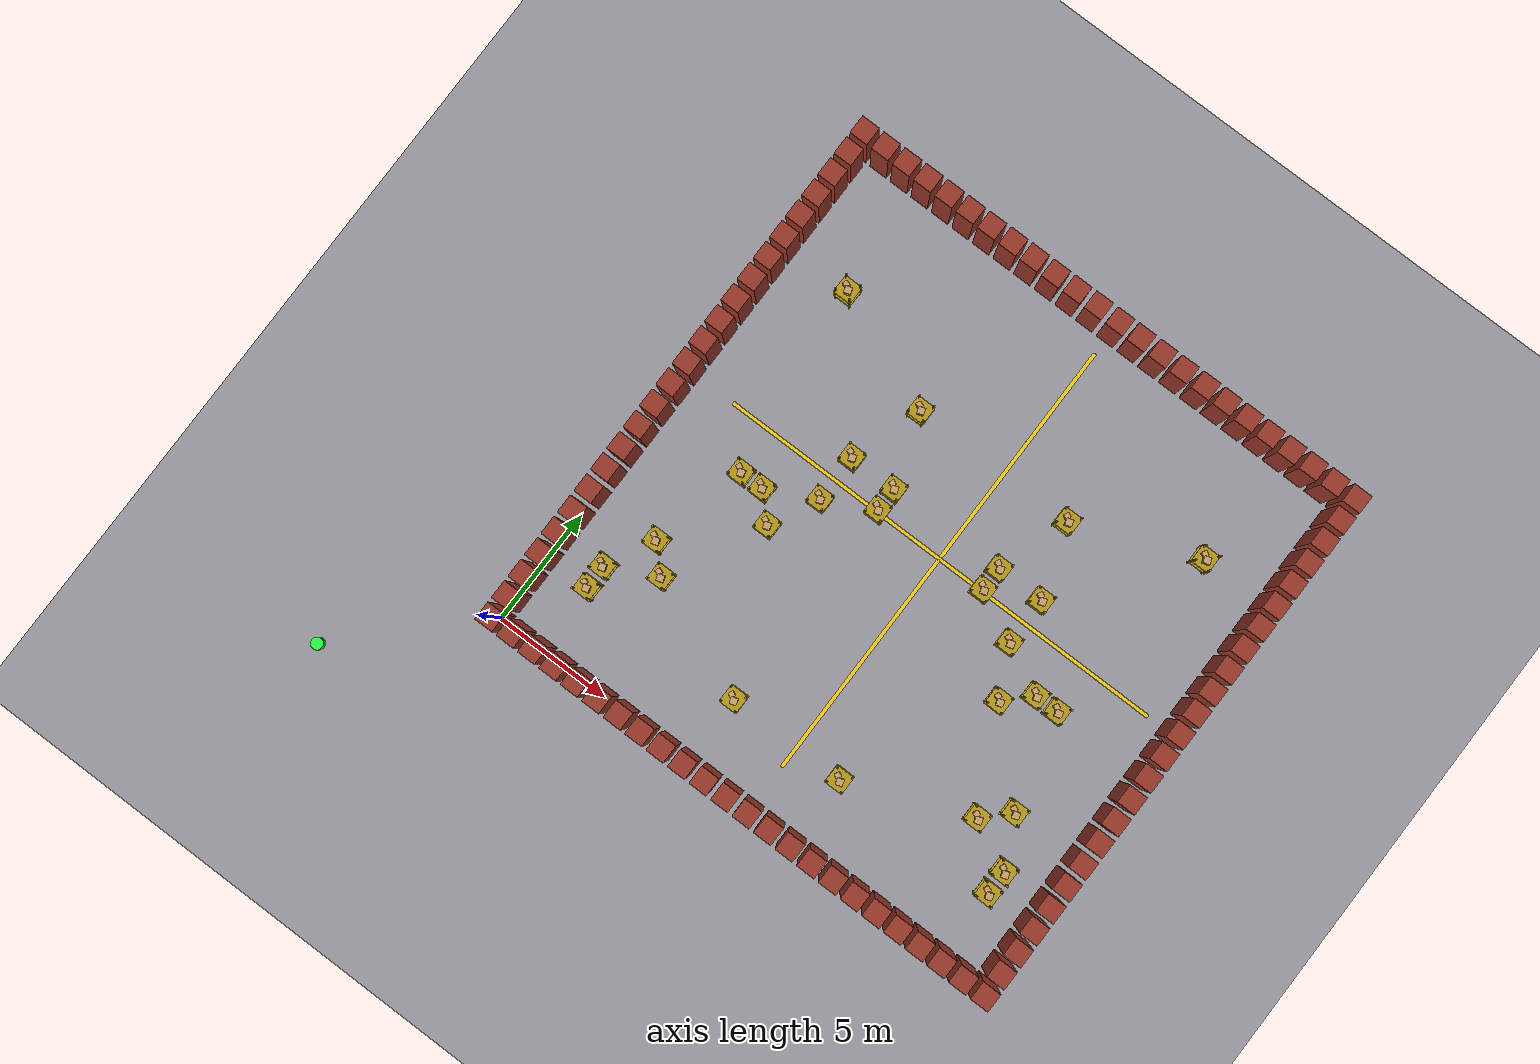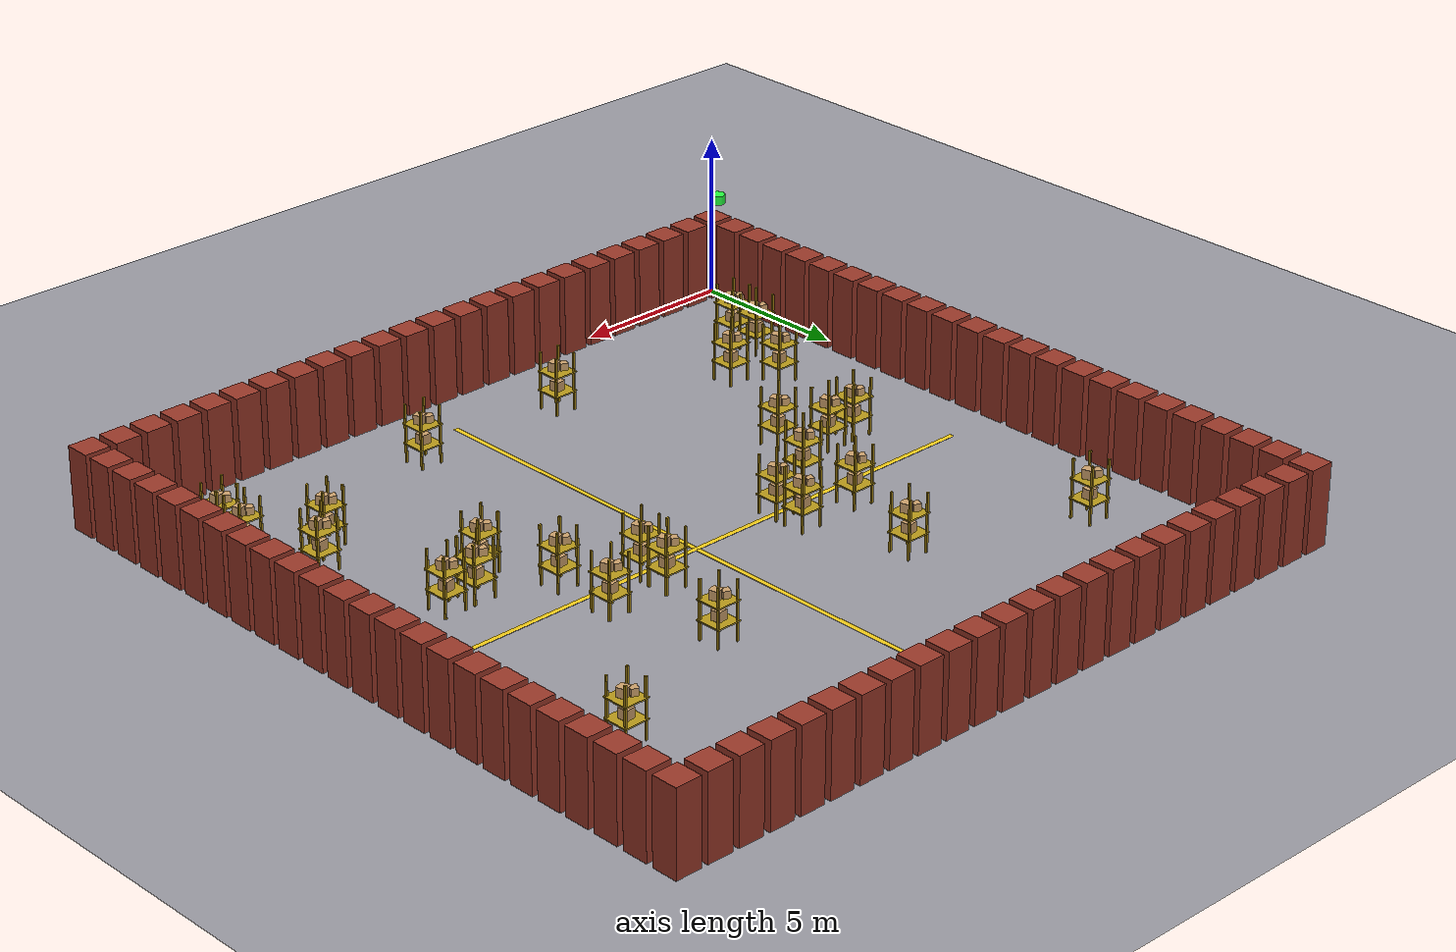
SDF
<sdf version="1.9">
 <world name="agv_nav">
  <physics name="1ms" type="ignored">
   <max_step_size>0.004</max_step_size>
   <real_time_factor>0</real_time_factor>
  </physics>
  <plugin filename="gz-sim-physics-system" name="gz::sim::systems::Physics"/>
  <plugin filename="gz-sim-user-commands-system" name="gz::sim::systems::UserCommands"/>
  <plugin filename="gz-sim-scene-broadcaster-system" name="gz::sim::systems::SceneBroadcaster"/>
  <plugin filename="gz-sim-contact-system" name="gz::sim::systems::Contact"/>
  <light type="directional" name="sun">
   <cast_shadows>false</cast_shadows>
   <pose>0 0 10 0 0 0</pose>
   <direction>-0.5 0.1 -0.9</direction>
   <diffuse>0.9 0.9 0.85 1</diffuse>
  </light>
  <model name="goal_marker">
   <static>false</static>
   <pose>-5 -5 0.15 0 0 0</pose>
   <link name="link">
    <gravity>false</gravity>
    <visual name="visual">
     <geometry><cylinder><radius>0.25</radius><length>0.3</length></cylinder></geometry>
     <material>
      <ambient>0.1 0.9 0.2 1</ambient>
      <diffuse>0.15 1.0 0.25 1</diffuse>
      <emissive>0.05 0.5 0.05 1</emissive>
     </material>
    </visual>
   </link>
  </model>
  <model name="ground_plane">
   <static>true</static>
   <link name="link">
    <collision name="collision">
     <geometry><plane><normal>0 0 1</normal><size>100 100</size></plane></geometry>
    </collision>
    <visual name="visual">
     <geometry><plane><normal>0 0 1</normal><size>100 100</size></plane></geometry>
     <material>
      <ambient>0.55 0.55 0.58 1</ambient>
      <diffuse>0.6 0.6 0.63 1</diffuse>
      <specular>0.2 0.2 0.2 1</specular>
     </material>
    </visual>
   </link>
  </model>
  <model name="wall_0">
   <static>true</static>
   <pose>0 0 1.25 0 0 0</pose>
   <link name="link">
    <collision name="collision"><geometry><box><size>0.8 0.8 2.5</size></box></geometry></collision>
    <visual name="visual">
     <geometry><box><size>0.8 0.8 2.5</size></box></geometry>
     <material>
      <ambient>0.5 0.18 0.14 1</ambient>
      <diffuse>0.6 0.22 0.16 1</diffuse>
      <specular>0.1 0.1 0.1 1</specular>
     </material>
    </visual>
   </link>
  </model>
  <model name="wall_1">
   <static>true</static>
   <pose>1 0 1.25 0 0 0</pose>
   <link name="link">
    <collision name="collision"><geometry><box><size>0.8 0.8 2.5</size></box></geometry></collision>
    <visual name="visual">
     <geometry><box><size>0.8 0.8 2.5</size></box></geometry>
     <material>
      <ambient>0.5 0.18 0.14 1</ambient>
      <diffuse>0.6 0.22 0.16 1</diffuse>
      <specular>0.1 0.1 0.1 1</specular>
     </material>
    </visual>
   </link>
  </model>
  <model name="wall_2">
   <static>true</static>
   <pose>2 0 1.25 0 0 0</pose>
   <link name="link">
    <collision name="collision"><geometry><box><size>0.8 0.8 2.5</size></box></geometry></collision>
    <visual name="visual">
     <geometry><box><size>0.8 0.8 2.5</size></box></geometry>
     <material>
      <ambient>0.5 0.18 0.14 1</ambient>
      <diffuse>0.6 0.22 0.16 1</diffuse>
      <specular>0.1 0.1 0.1 1</specular>
     </material>
    </visual>
   </link>
  </model>
  <model name="wall_3">
   <static>true</static>
   <pose>3 0 1.25 0 0 0</pose>
   <link name="link">
    <collision name="collision"><geometry><box><size>0.8 0.8 2.5</size></box></geometry></collision>
    <visual name="visual">
     <geometry><box><size>0.8 0.8 2.5</size></box></geometry>
     <material>
      <ambient>0.5 0.18 0.14 1</ambient>
      <diffuse>0.6 0.22 0.16 1</diffuse>
      <specular>0.1 0.1 0.1 1</specular>
     </material>
    </visual>
   </link>
  </model>
  <model name="wall_4">
   <static>true</static>
   <pose>4 0 1.25 0 0 0</pose>
   <link name="link">
    <collision name="collision"><geometry><box><size>0.8 0.8 2.5</size></box></geometry></collision>
    <visual name="visual">
     <geometry><box><size>0.8 0.8 2.5</size></box></geometry>
     <material>
      <ambient>0.5 0.18 0.14 1</ambient>
      <diffuse>0.6 0.22 0.16 1</diffuse>
      <specular>0.1 0.1 0.1 1</specular>
     </material>
    </visual>
   </link>
  </model>
  <model name="wall_5">
   <static>true</static>
   <pose>5 0 1.25 0 0 0</pose>
   <link name="link">
    <collision name="collision"><geometry><box><size>0.8 0.8 2.5</size></box></geometry></collision>
    <visual name="visual">
     <geometry><box><size>0.8 0.8 2.5</size></box></geometry>
     <material>
      <ambient>0.5 0.18 0.14 1</ambient>
      <diffuse>0.6 0.22 0.16 1</diffuse>
      <specular>0.1 0.1 0.1 1</specular>
     </material>
    </visual>
   </link>
  </model>
  <model name="wall_6">
   <static>true</static>
   <pose>6 0 1.25 0 0 0</pose>
   <link name="link">
    <collision name="collision"><geometry><box><size>0.8 0.8 2.5</size></box></geometry></collision>
    <visual name="visual">
     <geometry><box><size>0.8 0.8 2.5</size></box></geometry>
     <material>
      <ambient>0.5 0.18 0.14 1</ambient>
      <diffuse>0.6 0.22 0.16 1</diffuse>
      <specular>0.1 0.1 0.1 1</specular>
     </material>
    </visual>
   </link>
  </model>
  <model name="wall_7">
   <static>true</static>
   <pose>7 0 1.25 0 0 0</pose>
   <link name="link">
    <collision name="collision"><geometry><box><size>0.8 0.8 2.5</size></box></geometry></collision>
    <visual name="visual">
     <geometry><box><size>0.8 0.8 2.5</size></box></geometry>
     <material>
      <ambient>0.5 0.18 0.14 1</ambient>
      <diffuse>0.6 0.22 0.16 1</diffuse>
      <specular>0.1 0.1 0.1 1</specular>
     </material>
    </visual>
   </link>
  </model>
  <model name="wall_8">
   <static>true</static>
   <pose>8 0 1.25 0 0 0</pose>
   <link name="link">
    <collision name="collision"><geometry><box><size>0.8 0.8 2.5</size></box></geometry></collision>
    <visual name="visual">
     <geometry><box><size>0.8 0.8 2.5</size></box></geometry>
     <material>
      <ambient>0.5 0.18 0.14 1</ambient>
      <diffuse>0.6 0.22 0.16 1</diffuse>
      <specular>0.1 0.1 0.1 1</specular>
     </material>
    </visual>
   </link>
  </model>
  <model name="wall_9">
   <static>true</static>
   <pose>9 0 1.25 0 0 0</pose>
   <link name="link">
    <collision name="collision"><geometry><box><size>0.8 0.8 2.5</size></box></geometry></collision>
    <visual name="visual">
     <geometry><box><size>0.8 0.8 2.5</size></box></geometry>
     <material>
      <ambient>0.5 0.18 0.14 1</ambient>
      <diffuse>0.6 0.22 0.16 1</diffuse>
      <specular>0.1 0.1 0.1 1</specular>
     </material>
    </visual>
   </link>
  </model>
  <model name="wall_10">
   <static>true</static>
   <pose>10 0 1.25 0 0 0</pose>
   <link name="link">
    <collision name="collision"><geometry><box><size>0.8 0.8 2.5</size></box></geometry></collision>
    <visual name="visual">
     <geometry><box><size>0.8 0.8 2.5</size></box></geometry>
     <material>
      <ambient>0.5 0.18 0.14 1</ambient>
      <diffuse>0.6 0.22 0.16 1</diffuse>
      <specular>0.1 0.1 0.1 1</specular>
     </material>
    </visual>
   </link>
  </model>
  <model name="wall_11">
   <static>true</static>
   <pose>11 0 1.25 0 0 0</pose>
   <link name="link">
    <collision name="collision"><geometry><box><size>0.8 0.8 2.5</size></box></geometry></collision>
    <visual name="visual">
     <geometry><box><size>0.8 0.8 2.5</size></box></geometry>
     <material>
      <ambient>0.5 0.18 0.14 1</ambient>
      <diffuse>0.6 0.22 0.16 1</diffuse>
      <specular>0.1 0.1 0.1 1</specular>
     </material>
    </visual>
   </link>
  </model>
  <model name="wall_12">
   <static>true</static>
   <pose>12 0 1.25 0 0 0</pose>
   <link name="link">
    <collision name="collision"><geometry><box><size>0.8 0.8 2.5</size></box></geometry></collision>
    <visual name="visual">
     <geometry><box><size>0.8 0.8 2.5</size></box></geometry>
     <material>
      <ambient>0.5 0.18 0.14 1</ambient>
      <diffuse>0.6 0.22 0.16 1</diffuse>
      <specular>0.1 0.1 0.1 1</specular>
     </material>
    </visual>
   </link>
  </model>
  <model name="wall_13">
   <static>true</static>
   <pose>13 0 1.25 0 0 0</pose>
   <link name="link">
    <collision name="collision"><geometry><box><size>0.8 0.8 2.5</size></box></geometry></collision>
    <visual name="visual">
     <geometry><box><size>0.8 0.8 2.5</size></box></geometry>
     <material>
      <ambient>0.5 0.18 0.14 1</ambient>
      <diffuse>0.6 0.22 0.16 1</diffuse>
      <specular>0.1 0.1 0.1 1</specular>
     </material>
    </visual>
   </link>
  </model>
  <model name="wall_14">
   <static>true</static>
   <pose>14 0 1.25 0 0 0</pose>
   <link name="link">
    <collision name="collision"><geometry><box><size>0.8 0.8 2.5</size></box></geometry></collision>
    <visual name="visual">
     <geometry><box><size>0.8 0.8 2.5</size></box></geometry>
     <material>
      <ambient>0.5 0.18 0.14 1</ambient>
      <diffuse>0.6 0.22 0.16 1</diffuse>
      <specular>0.1 0.1 0.1 1</specular>
     </material>
    </visual>
   </link>
  </model>
  <model name="wall_15">
   <static>true</static>
   <pose>15 0 1.25 0 0 0</pose>
   <link name="link">
    <collision name="collision"><geometry><box><size>0.8 0.8 2.5</size></box></geometry></collision>
    <visual name="visual">
     <geometry><box><size>0.8 0.8 2.5</size></box></geometry>
     <material>
      <ambient>0.5 0.18 0.14 1</ambient>
      <diffuse>0.6 0.22 0.16 1</diffuse>
      <specular>0.1 0.1 0.1 1</specular>
     </material>
    </visual>
   </link>
  </model>
  <model name="wall_16">
   <static>true</static>
   <pose>16 0 1.25 0 0 0</pose>
   <link name="link">
    <collision name="collision"><geometry><box><size>0.8 0.8 2.5</size></box></geometry></collision>
    <visual name="visual">
     <geometry><box><size>0.8 0.8 2.5</size></box></geometry>
     <material>
      <ambient>0.5 0.18 0.14 1</ambient>
      <diffuse>0.6 0.22 0.16 1</diffuse>
      <specular>0.1 0.1 0.1 1</specular>
     </material>
    </visual>
   </link>
  </model>
  <model name="wall_17">
   <static>true</static>
   <pose>17 0 1.25 0 0 0</pose>
   <link name="link">
    <collision name="collision"><geometry><box><size>0.8 0.8 2.5</size></box></geometry></collision>
    <visual name="visual">
     <geometry><box><size>0.8 0.8 2.5</size></box></geometry>
     <material>
      <ambient>0.5 0.18 0.14 1</ambient>
      <diffuse>0.6 0.22 0.16 1</diffuse>
      <specular>0.1 0.1 0.1 1</specular>
     </material>
    </visual>
   </link>
  </model>
  <model name="wall_18">
   <static>true</static>
   <pose>18 0 1.25 0 0 0</pose>
   <link name="link">
    <collision name="collision"><geometry><box><size>0.8 0.8 2.5</size></box></geometry></collision>
    <visual name="visual">
     <geometry><box><size>0.8 0.8 2.5</size></box></geometry>
     <material>
      <ambient>0.5 0.18 0.14 1</ambient>
      <diffuse>0.6 0.22 0.16 1</diffuse>
      <specular>0.1 0.1 0.1 1</specular>
     </material>
    </visual>
   </link>
  </model>
  <model name="wall_19">
   <static>true</static>
   <pose>19 0 1.25 0 0 0</pose>
   <link name="link">
    <collision name="collision"><geometry><box><size>0.8 0.8 2.5</size></box></geometry></collision>
    <visual name="visual">
     <geometry><box><size>0.8 0.8 2.5</size></box></geometry>
     <material>
      <ambient>0.5 0.18 0.14 1</ambient>
      <diffuse>0.6 0.22 0.16 1</diffuse>
      <specular>0.1 0.1 0.1 1</specular>
     </material>
    </visual>
   </link>
  </model>
  <model name="wall_20">
   <static>true</static>
   <pose>20 0 1.25 0 0 0</pose>
   <link name="link">
    <collision name="collision"><geometry><box><size>0.8 0.8 2.5</size></box></geometry></collision>
    <visual name="visual">
     <geometry><box><size>0.8 0.8 2.5</size></box></geometry>
     <material>
      <ambient>0.5 0.18 0.14 1</ambient>
      <diffuse>0.6 0.22 0.16 1</diffuse>
      <specular>0.1 0.1 0.1 1</specular>
     </material>
    </visual>
   </link>
  </model>
  <model name="wall_21">
   <static>true</static>
   <pose>21 0 1.25 0 0 0</pose>
   <link name="link">
    <collision name="collision"><geometry><box><size>0.8 0.8 2.5</size></box></geometry></collision>
    <visual name="visual">
     <geometry><box><size>0.8 0.8 2.5</size></box></geometry>
     <material>
      <ambient>0.5 0.18 0.14 1</ambient>
      <diffuse>0.6 0.22 0.16 1</diffuse>
      <specular>0.1 0.1 0.1 1</specular>
     </material>
    </visual>
   </link>
  </model>
  <model name="wall_22">
   <static>true</static>
   <pose>22 0 1.25 0 0 0</pose>
   <link name="link">
    <collision name="collision"><geometry><box><size>0.8 0.8 2.5</size></box></geometry></collision>
    <visual name="visual">
     <geometry><box><size>0.8 0.8 2.5</size></box></geometry>
     <material>
      <ambient>0.5 0.18 0.14 1</ambient>
      <diffuse>0.6 0.22 0.16 1</diffuse>
      <specular>0.1 0.1 0.1 1</specular>
     </material>
    </visual>
   </link>
  </model>
  <model name="wall_23">
   <static>true</static>
   <pose>23 0 1.25 0 0 0</pose>
   <link name="link">
    <collision name="collision"><geometry><box><size>0.8 0.8 2.5</size></box></geometry></collision>
    <visual name="visual">
     <geometry><box><size>0.8 0.8 2.5</size></box></geometry>
     <material>
      <ambient>0.5 0.18 0.14 1</ambient>
      <diffuse>0.6 0.22 0.16 1</diffuse>
      <specular>0.1 0.1 0.1 1</specular>
     </material>
    </visual>
   </link>
  </model>
  <model name="wall_24">
   <static>true</static>
   <pose>0 1 1.25 0 0 0</pose>
   <link name="link">
    <collision name="collision"><geometry><box><size>0.8 0.8 2.5</size></box></geometry></collision>
    <visual name="visual">
     <geometry><box><size>0.8 0.8 2.5</size></box></geometry>
     <material>
      <ambient>0.5 0.18 0.14 1</ambient>
      <diffuse>0.6 0.22 0.16 1</diffuse>
      <specular>0.1 0.1 0.1 1</specular>
     </material>
    </visual>
   </link>
  </model>
  <model name="wall_25">
   <static>true</static>
   <pose>23 1 1.25 0 0 0</pose>
   <link name="link">
    <collision name="collision"><geometry><box><size>0.8 0.8 2.5</size></box></geometry></collision>
    <visual name="visual">
     <geometry><box><size>0.8 0.8 2.5</size></box></geometry>
     <material>
      <ambient>0.5 0.18 0.14 1</ambient>
      <diffuse>0.6 0.22 0.16 1</diffuse>
      <specular>0.1 0.1 0.1 1</specular>
     </material>
    </visual>
   </link>
  </model>
  <model name="wall_26">
   <static>true</static>
   <pose>0 2 1.25 0 0 0</pose>
   <link name="link">
    <collision name="collision"><geometry><box><size>0.8 0.8 2.5</size></box></geometry></collision>
    <visual name="visual">
     <geometry><box><size>0.8 0.8 2.5</size></box></geometry>
     <material>
      <ambient>0.5 0.18 0.14 1</ambient>
      <diffuse>0.6 0.22 0.16 1</diffuse>
      <specular>0.1 0.1 0.1 1</specular>
     </material>
    </visual>
   </link>
  </model>
  <model name="wall_27">
   <static>true</static>
   <pose>23 2 1.25 0 0 0</pose>
   <link name="link">
    <collision name="collision"><geometry><box><size>0.8 0.8 2.5</size></box></geometry></collision>
    <visual name="visual">
     <geometry><box><size>0.8 0.8 2.5</size></box></geometry>
     <material>
      <ambient>0.5 0.18 0.14 1</ambient>
      <diffuse>0.6 0.22 0.16 1</diffuse>
      <specular>0.1 0.1 0.1 1</specular>
     </material>
    </visual>
   </link>
  </model>
  <model name="wall_28">
   <static>true</static>
   <pose>0 3 1.25 0 0 0</pose>
   <link name="link">
    <collision name="collision"><geometry><box><size>0.8 0.8 2.5</size></box></geometry></collision>
    <visual name="visual">
     <geometry><box><size>0.8 0.8 2.5</size></box></geometry>
     <material>
      <ambient>0.5 0.18 0.14 1</ambient>
      <diffuse>0.6 0.22 0.16 1</diffuse>
      <specular>0.1 0.1 0.1 1</specular>
     </material>
    </visual>
   </link>
  </model>
  <model name="obs_0">
   <static>true</static>
   <pose>2 3 0.9 0 0 0</pose>
   <link name="link">
    <collision name="collision"><geometry><box><size>0.8 0.8 1.8</size></box></geometry></collision>
    <visual name="post_0">
     <pose>0.34 0.34 0 0 0 0</pose>
     <geometry><box><size>0.06 0.06 1.8</size></box></geometry>
     <material><ambient>0.55 0.45 0.05 1</ambient><diffuse>0.65 0.52 0.06 1</diffuse></material>
    </visual>
    <visual name="post_1">
     <pose>-0.34 0.34 0 0 0 0</pose>
     <geometry><box><size>0.06 0.06 1.8</size></box></geometry>
     <material><ambient>0.55 0.45 0.05 1</ambient><diffuse>0.65 0.52 0.06 1</diffuse></material>
    </visual>
    <visual name="post_2">
     <pose>0.34 -0.34 0 0 0 0</pose>
     <geometry><box><size>0.06 0.06 1.8</size></box></geometry>
     <material><ambient>0.55 0.45 0.05 1</ambient><diffuse>0.65 0.52 0.06 1</diffuse></material>
    </visual>
    <visual name="post_3">
     <pose>-0.34 -0.34 0 0 0 0</pose>
     <geometry><box><size>0.06 0.06 1.8</size></box></geometry>
     <material><ambient>0.55 0.45 0.05 1</ambient><diffuse>0.65 0.52 0.06 1</diffuse></material>
    </visual>
    <visual name="plank_0">
     <pose>0 0 -0.3 0 0 0</pose>
     <geometry><box><size>0.8 0.8 0.04</size></box></geometry>
     <material><ambient>0.6 0.5 0.08 1</ambient><diffuse>0.72 0.6 0.1 1</diffuse></material>
    </visual>
    <visual name="plank_1">
     <pose>0 0 0.3 0 0 0</pose>
     <geometry><box><size>0.8 0.8 0.04</size></box></geometry>
     <material><ambient>0.6 0.5 0.08 1</ambient><diffuse>0.72 0.6 0.1 1</diffuse></material>
    </visual>
    <visual name="cbox_0">
     <pose>0.05 -0.05 0.47 0 0 0.3</pose>
     <geometry><box><size>0.28 0.28 0.28</size></box></geometry>
     <material><ambient>0.72 0.56 0.38 1</ambient><diffuse>0.8 0.63 0.42 1</diffuse></material>
    </visual>
    <visual name="cbox_1">
     <pose>-0.15 0.1 0.47 0 0 -0.4</pose>
     <geometry><box><size>0.22 0.22 0.22</size></box></geometry>
     <material><ambient>0.72 0.56 0.38 1</ambient><diffuse>0.8 0.63 0.42 1</diffuse></material>
    </visual>
    <visual name="cbox_2">
     <pose>0.0 0.0 -0.13 0 0 0.1</pose>
     <geometry><box><size>0.3 0.3 0.3</size></box></geometry>
     <material><ambient>0.72 0.56 0.38 1</ambient><diffuse>0.8 0.63 0.42 1</diffuse></material>
    </visual>
   </link>
  </model>
  <model name="obs_1">
   <static>true</static>
   <pose>9 3 0.9 0 0 0</pose>
   <link name="link">
    <collision name="collision"><geometry><box><size>0.8 0.8 1.8</size></box></geometry></collision>
    <visual name="post_0">
     <pose>0.34 0.34 0 0 0 0</pose>
     <geometry><box><size>0.06 0.06 1.8</size></box></geometry>
     <material><ambient>0.55 0.45 0.05 1</ambient><diffuse>0.65 0.52 0.06 1</diffuse></material>
    </visual>
    <visual name="post_1">
     <pose>-0.34 0.34 0 0 0 0</pose>
     <geometry><box><size>0.06 0.06 1.8</size></box></geometry>
     <material><ambient>0.55 0.45 0.05 1</ambient><diffuse>0.65 0.52 0.06 1</diffuse></material>
    </visual>
    <visual name="post_2">
     <pose>0.34 -0.34 0 0 0 0</pose>
     <geometry><box><size>0.06 0.06 1.8</size></box></geometry>
     <material><ambient>0.55 0.45 0.05 1</ambient><diffuse>0.65 0.52 0.06 1</diffuse></material>
    </visual>
    <visual name="post_3">
     <pose>-0.34 -0.34 0 0 0 0</pose>
     <geometry><box><size>0.06 0.06 1.8</size></box></geometry>
     <material><ambient>0.55 0.45 0.05 1</ambient><diffuse>0.65 0.52 0.06 1</diffuse></material>
    </visual>
    <visual name="plank_0">
     <pose>0 0 -0.3 0 0 0</pose>
     <geometry><box><size>0.8 0.8 0.04</size></box></geometry>
     <material><ambient>0.6 0.5 0.08 1</ambient><diffuse>0.72 0.6 0.1 1</diffuse></material>
    </visual>
    <visual name="plank_1">
     <pose>0 0 0.3 0 0 0</pose>
     <geometry><box><size>0.8 0.8 0.04</size></box></geometry>
     <material><ambient>0.6 0.5 0.08 1</ambient><diffuse>0.72 0.6 0.1 1</diffuse></material>
    </visual>
    <visual name="cbox_0">
     <pose>0.05 -0.05 0.47 0 0 0.3</pose>
     <geometry><box><size>0.28 0.28 0.28</size></box></geometry>
     <material><ambient>0.72 0.56 0.38 1</ambient><diffuse>0.8 0.63 0.42 1</diffuse></material>
    </visual>
    <visual name="cbox_1">
     <pose>-0.15 0.1 0.47 0 0 -0.4</pose>
     <geometry><box><size>0.22 0.22 0.22</size></box></geometry>
     <material><ambient>0.72 0.56 0.38 1</ambient><diffuse>0.8 0.63 0.42 1</diffuse></material>
    </visual>
    <visual name="cbox_2">
     <pose>0.0 0.0 -0.13 0 0 0.1</pose>
     <geometry><box><size>0.3 0.3 0.3</size></box></geometry>
     <material><ambient>0.72 0.56 0.38 1</ambient><diffuse>0.8 0.63 0.42 1</diffuse></material>
    </visual>
   </link>
  </model>
  <model name="obs_2">
   <static>true</static>
   <pose>14 3 0.9 0 0 0</pose>
   <link name="link">
    <collision name="collision"><geometry><box><size>0.8 0.8 1.8</size></box></geometry></collision>
    <visual name="post_0">
     <pose>0.34 0.34 0 0 0 0</pose>
     <geometry><box><size>0.06 0.06 1.8</size></box></geometry>
     <material><ambient>0.55 0.45 0.05 1</ambient><diffuse>0.65 0.52 0.06 1</diffuse></material>
    </visual>
    <visual name="post_1">
     <pose>-0.34 0.34 0 0 0 0</pose>
     <geometry><box><size>0.06 0.06 1.8</size></box></geometry>
     <material><ambient>0.55 0.45 0.05 1</ambient><diffuse>0.65 0.52 0.06 1</diffuse></material>
    </visual>
    <visual name="post_2">
     <pose>0.34 -0.34 0 0 0 0</pose>
     <geometry><box><size>0.06 0.06 1.8</size></box></geometry>
     <material><ambient>0.55 0.45 0.05 1</ambient><diffuse>0.65 0.52 0.06 1</diffuse></material>
    </visual>
    <visual name="post_3">
     <pose>-0.34 -0.34 0 0 0 0</pose>
     <geometry><box><size>0.06 0.06 1.8</size></box></geometry>
     <material><ambient>0.55 0.45 0.05 1</ambient><diffuse>0.65 0.52 0.06 1</diffuse></material>
    </visual>
    <visual name="plank_0">
     <pose>0 0 -0.3 0 0 0</pose>
     <geometry><box><size>0.8 0.8 0.04</size></box></geometry>
     <material><ambient>0.6 0.5 0.08 1</ambient><diffuse>0.72 0.6 0.1 1</diffuse></material>
    </visual>
    <visual name="plank_1">
     <pose>0 0 0.3 0 0 0</pose>
     <geometry><box><size>0.8 0.8 0.04</size></box></geometry>
     <material><ambient>0.6 0.5 0.08 1</ambient><diffuse>0.72 0.6 0.1 1</diffuse></material>
    </visual>
    <visual name="cbox_0">
     <pose>0.05 -0.05 0.47 0 0 0.3</pose>
     <geometry><box><size>0.28 0.28 0.28</size></box></geometry>
     <material><ambient>0.72 0.56 0.38 1</ambient><diffuse>0.8 0.63 0.42 1</diffuse></material>
    </visual>
    <visual name="cbox_1">
     <pose>-0.15 0.1 0.47 0 0 -0.4</pose>
     <geometry><box><size>0.22 0.22 0.22</size></box></geometry>
     <material><ambient>0.72 0.56 0.38 1</ambient><diffuse>0.8 0.63 0.42 1</diffuse></material>
    </visual>
    <visual name="cbox_2">
     <pose>0.0 0.0 -0.13 0 0 0.1</pose>
     <geometry><box><size>0.3 0.3 0.3</size></box></geometry>
     <material><ambient>0.72 0.56 0.38 1</ambient><diffuse>0.8 0.63 0.42 1</diffuse></material>
    </visual>
   </link>
  </model>
  <model name="obs_3">
   <static>true</static>
   <pose>21 3 0.9 0 0 0</pose>
   <link name="link">
    <collision name="collision"><geometry><box><size>0.8 0.8 1.8</size></box></geometry></collision>
    <visual name="post_0">
     <pose>0.34 0.34 0 0 0 0</pose>
     <geometry><box><size>0.06 0.06 1.8</size></box></geometry>
     <material><ambient>0.55 0.45 0.05 1</ambient><diffuse>0.65 0.52 0.06 1</diffuse></material>
    </visual>
    <visual name="post_1">
     <pose>-0.34 0.34 0 0 0 0</pose>
     <geometry><box><size>0.06 0.06 1.8</size></box></geometry>
     <material><ambient>0.55 0.45 0.05 1</ambient><diffuse>0.65 0.52 0.06 1</diffuse></material>
    </visual>
    <visual name="post_2">
     <pose>0.34 -0.34 0 0 0 0</pose>
     <geometry><box><size>0.06 0.06 1.8</size></box></geometry>
     <material><ambient>0.55 0.45 0.05 1</ambient><diffuse>0.65 0.52 0.06 1</diffuse></material>
    </visual>
    <visual name="post_3">
     <pose>-0.34 -0.34 0 0 0 0</pose>
     <geometry><box><size>0.06 0.06 1.8</size></box></geometry>
     <material><ambient>0.55 0.45 0.05 1</ambient><diffuse>0.65 0.52 0.06 1</diffuse></material>
    </visual>
    <visual name="plank_0">
     <pose>0 0 -0.3 0 0 0</pose>
     <geometry><box><size>0.8 0.8 0.04</size></box></geometry>
     <material><ambient>0.6 0.5 0.08 1</ambient><diffuse>0.72 0.6 0.1 1</diffuse></material>
    </visual>
    <visual name="plank_1">
     <pose>0 0 0.3 0 0 0</pose>
     <geometry><box><size>0.8 0.8 0.04</size></box></geometry>
     <material><ambient>0.6 0.5 0.08 1</ambient><diffuse>0.72 0.6 0.1 1</diffuse></material>
    </visual>
    <visual name="cbox_0">
     <pose>0.05 -0.05 0.47 0 0 0.3</pose>
     <geometry><box><size>0.28 0.28 0.28</size></box></geometry>
     <material><ambient>0.72 0.56 0.38 1</ambient><diffuse>0.8 0.63 0.42 1</diffuse></material>
    </visual>
    <visual name="cbox_1">
     <pose>-0.15 0.1 0.47 0 0 -0.4</pose>
     <geometry><box><size>0.22 0.22 0.22</size></box></geometry>
     <material><ambient>0.72 0.56 0.38 1</ambient><diffuse>0.8 0.63 0.42 1</diffuse></material>
    </visual>
    <visual name="cbox_2">
     <pose>0.0 0.0 -0.13 0 0 0.1</pose>
     <geometry><box><size>0.3 0.3 0.3</size></box></geometry>
     <material><ambient>0.72 0.56 0.38 1</ambient><diffuse>0.8 0.63 0.42 1</diffuse></material>
    </visual>
   </link>
  </model>
  <model name="wall_29">
   <static>true</static>
   <pose>23 3 1.25 0 0 0</pose>
   <link name="link">
    <collision name="collision"><geometry><box><size>0.8 0.8 2.5</size></box></geometry></collision>
    <visual name="visual">
     <geometry><box><size>0.8 0.8 2.5</size></box></geometry>
     <material>
      <ambient>0.5 0.18 0.14 1</ambient>
      <diffuse>0.6 0.22 0.16 1</diffuse>
      <specular>0.1 0.1 0.1 1</specular>
     </material>
    </visual>
   </link>
  </model>
  <model name="wall_30">
   <static>true</static>
   <pose>0 4 1.25 0 0 0</pose>
   <link name="link">
    <collision name="collision"><geometry><box><size>0.8 0.8 2.5</size></box></geometry></collision>
    <visual name="visual">
     <geometry><box><size>0.8 0.8 2.5</size></box></geometry>
     <material>
      <ambient>0.5 0.18 0.14 1</ambient>
      <diffuse>0.6 0.22 0.16 1</diffuse>
      <specular>0.1 0.1 0.1 1</specular>
     </material>
    </visual>
   </link>
  </model>
  <model name="obs_4">
   <static>true</static>
   <pose>2 4 0.9 0 0 0</pose>
   <link name="link">
    <collision name="collision"><geometry><box><size>0.8 0.8 1.8</size></box></geometry></collision>
    <visual name="post_0">
     <pose>0.34 0.34 0 0 0 0</pose>
     <geometry><box><size>0.06 0.06 1.8</size></box></geometry>
     <material><ambient>0.55 0.45 0.05 1</ambient><diffuse>0.65 0.52 0.06 1</diffuse></material>
    </visual>
    <visual name="post_1">
     <pose>-0.34 0.34 0 0 0 0</pose>
     <geometry><box><size>0.06 0.06 1.8</size></box></geometry>
     <material><ambient>0.55 0.45 0.05 1</ambient><diffuse>0.65 0.52 0.06 1</diffuse></material>
    </visual>
    <visual name="post_2">
     <pose>0.34 -0.34 0 0 0 0</pose>
     <geometry><box><size>0.06 0.06 1.8</size></box></geometry>
     <material><ambient>0.55 0.45 0.05 1</ambient><diffuse>0.65 0.52 0.06 1</diffuse></material>
    </visual>
    <visual name="post_3">
     <pose>-0.34 -0.34 0 0 0 0</pose>
     <geometry><box><size>0.06 0.06 1.8</size></box></geometry>
     <material><ambient>0.55 0.45 0.05 1</ambient><diffuse>0.65 0.52 0.06 1</diffuse></material>
    </visual>
    <visual name="plank_0">
     <pose>0 0 -0.3 0 0 0</pose>
     <geometry><box><size>0.8 0.8 0.04</size></box></geometry>
     <material><ambient>0.6 0.5 0.08 1</ambient><diffuse>0.72 0.6 0.1 1</diffuse></material>
    </visual>
    <visual name="plank_1">
     <pose>0 0 0.3 0 0 0</pose>
     <geometry><box><size>0.8 0.8 0.04</size></box></geometry>
     <material><ambient>0.6 0.5 0.08 1</ambient><diffuse>0.72 0.6 0.1 1</diffuse></material>
    </visual>
    <visual name="cbox_0">
     <pose>0.05 -0.05 0.47 0 0 0.3</pose>
     <geometry><box><size>0.28 0.28 0.28</size></box></geometry>
     <material><ambient>0.72 0.56 0.38 1</ambient><diffuse>0.8 0.63 0.42 1</diffuse></material>
    </visual>
    <visual name="cbox_1">
     <pose>-0.15 0.1 0.47 0 0 -0.4</pose>
     <geometry><box><size>0.22 0.22 0.22</size></box></geometry>
     <material><ambient>0.72 0.56 0.38 1</ambient><diffuse>0.8 0.63 0.42 1</diffuse></material>
    </visual>
    <visual name="cbox_2">
     <pose>0.0 0.0 -0.13 0 0 0.1</pose>
     <geometry><box><size>0.3 0.3 0.3</size></box></geometry>
     <material><ambient>0.72 0.56 0.38 1</ambient><diffuse>0.8 0.63 0.42 1</diffuse></material>
    </visual>
   </link>
  </model>
  <model name="obs_5">
   <static>true</static>
   <pose>21 4 0.9 0 0 0</pose>
   <link name="link">
    <collision name="collision"><geometry><box><size>0.8 0.8 1.8</size></box></geometry></collision>
    <visual name="post_0">
     <pose>0.34 0.34 0 0 0 0</pose>
     <geometry><box><size>0.06 0.06 1.8</size></box></geometry>
     <material><ambient>0.55 0.45 0.05 1</ambient><diffuse>0.65 0.52 0.06 1</diffuse></material>
    </visual>
    <visual name="post_1">
     <pose>-0.34 0.34 0 0 0 0</pose>
     <geometry><box><size>0.06 0.06 1.8</size></box></geometry>
     <material><ambient>0.55 0.45 0.05 1</ambient><diffuse>0.65 0.52 0.06 1</diffuse></material>
    </visual>
    <visual name="post_2">
     <pose>0.34 -0.34 0 0 0 0</pose>
     <geometry><box><size>0.06 0.06 1.8</size></box></geometry>
     <material><ambient>0.55 0.45 0.05 1</ambient><diffuse>0.65 0.52 0.06 1</diffuse></material>
    </visual>
    <visual name="post_3">
     <pose>-0.34 -0.34 0 0 0 0</pose>
     <geometry><box><size>0.06 0.06 1.8</size></box></geometry>
     <material><ambient>0.55 0.45 0.05 1</ambient><diffuse>0.65 0.52 0.06 1</diffuse></material>
    </visual>
    <visual name="plank_0">
     <pose>0 0 -0.3 0 0 0</pose>
     <geometry><box><size>0.8 0.8 0.04</size></box></geometry>
     <material><ambient>0.6 0.5 0.08 1</ambient><diffuse>0.72 0.6 0.1 1</diffuse></material>
    </visual>
    <visual name="plank_1">
     <pose>0 0 0.3 0 0 0</pose>
     <geometry><box><size>0.8 0.8 0.04</size></box></geometry>
     <material><ambient>0.6 0.5 0.08 1</ambient><diffuse>0.72 0.6 0.1 1</diffuse></material>
    </visual>
    <visual name="cbox_0">
     <pose>0.05 -0.05 0.47 0 0 0.3</pose>
     <geometry><box><size>0.28 0.28 0.28</size></box></geometry>
     <material><ambient>0.72 0.56 0.38 1</ambient><diffuse>0.8 0.63 0.42 1</diffuse></material>
    </visual>
    <visual name="cbox_1">
     <pose>-0.15 0.1 0.47 0 0 -0.4</pose>
     <geometry><box><size>0.22 0.22 0.22</size></box></geometry>
     <material><ambient>0.72 0.56 0.38 1</ambient><diffuse>0.8 0.63 0.42 1</diffuse></material>
    </visual>
    <visual name="cbox_2">
     <pose>0.0 0.0 -0.13 0 0 0.1</pose>
     <geometry><box><size>0.3 0.3 0.3</size></box></geometry>
     <material><ambient>0.72 0.56 0.38 1</ambient><diffuse>0.8 0.63 0.42 1</diffuse></material>
    </visual>
   </link>
  </model>
  <model name="wall_31">
   <static>true</static>
   <pose>23 4 1.25 0 0 0</pose>
   <link name="link">
    <collision name="collision"><geometry><box><size>0.8 0.8 2.5</size></box></geometry></collision>
    <visual name="visual">
     <geometry><box><size>0.8 0.8 2.5</size></box></geometry>
     <material>
      <ambient>0.5 0.18 0.14 1</ambient>
      <diffuse>0.6 0.22 0.16 1</diffuse>
      <specular>0.1 0.1 0.1 1</specular>
     </material>
    </visual>
   </link>
  </model>
  <model name="wall_32">
   <static>true</static>
   <pose>0 5 1.25 0 0 0</pose>
   <link name="link">
    <collision name="collision"><geometry><box><size>0.8 0.8 2.5</size></box></geometry></collision>
    <visual name="visual">
     <geometry><box><size>0.8 0.8 2.5</size></box></geometry>
     <material>
      <ambient>0.5 0.18 0.14 1</ambient>
      <diffuse>0.6 0.22 0.16 1</diffuse>
      <specular>0.1 0.1 0.1 1</specular>
     </material>
    </visual>
   </link>
  </model>
  <model name="obs_6">
   <static>true</static>
   <pose>4 5 0.9 0 0 0</pose>
   <link name="link">
    <collision name="collision"><geometry><box><size>0.8 0.8 1.8</size></box></geometry></collision>
    <visual name="post_0">
     <pose>0.34 0.34 0 0 0 0</pose>
     <geometry><box><size>0.06 0.06 1.8</size></box></geometry>
     <material><ambient>0.55 0.45 0.05 1</ambient><diffuse>0.65 0.52 0.06 1</diffuse></material>
    </visual>
    <visual name="post_1">
     <pose>-0.34 0.34 0 0 0 0</pose>
     <geometry><box><size>0.06 0.06 1.8</size></box></geometry>
     <material><ambient>0.55 0.45 0.05 1</ambient><diffuse>0.65 0.52 0.06 1</diffuse></material>
    </visual>
    <visual name="post_2">
     <pose>0.34 -0.34 0 0 0 0</pose>
     <geometry><box><size>0.06 0.06 1.8</size></box></geometry>
     <material><ambient>0.55 0.45 0.05 1</ambient><diffuse>0.65 0.52 0.06 1</diffuse></material>
    </visual>
    <visual name="post_3">
     <pose>-0.34 -0.34 0 0 0 0</pose>
     <geometry><box><size>0.06 0.06 1.8</size></box></geometry>
     <material><ambient>0.55 0.45 0.05 1</ambient><diffuse>0.65 0.52 0.06 1</diffuse></material>
    </visual>
    <visual name="plank_0">
     <pose>0 0 -0.3 0 0 0</pose>
     <geometry><box><size>0.8 0.8 0.04</size></box></geometry>
     <material><ambient>0.6 0.5 0.08 1</ambient><diffuse>0.72 0.6 0.1 1</diffuse></material>
    </visual>
    <visual name="plank_1">
     <pose>0 0 0.3 0 0 0</pose>
     <geometry><box><size>0.8 0.8 0.04</size></box></geometry>
     <material><ambient>0.6 0.5 0.08 1</ambient><diffuse>0.72 0.6 0.1 1</diffuse></material>
    </visual>
    <visual name="cbox_0">
     <pose>0.05 -0.05 0.47 0 0 0.3</pose>
     <geometry><box><size>0.28 0.28 0.28</size></box></geometry>
     <material><ambient>0.72 0.56 0.38 1</ambient><diffuse>0.8 0.63 0.42 1</diffuse></material>
    </visual>
    <visual name="cbox_1">
     <pose>-0.15 0.1 0.47 0 0 -0.4</pose>
     <geometry><box><size>0.22 0.22 0.22</size></box></geometry>
     <material><ambient>0.72 0.56 0.38 1</ambient><diffuse>0.8 0.63 0.42 1</diffuse></material>
    </visual>
    <visual name="cbox_2">
     <pose>0.0 0.0 -0.13 0 0 0.1</pose>
     <geometry><box><size>0.3 0.3 0.3</size></box></geometry>
     <material><ambient>0.72 0.56 0.38 1</ambient><diffuse>0.8 0.63 0.42 1</diffuse></material>
    </visual>
   </link>
  </model>
  <model name="obs_7">
   <static>true</static>
   <pose>19 5 0.9 0 0 0</pose>
   <link name="link">
    <collision name="collision"><geometry><box><size>0.8 0.8 1.8</size></box></geometry></collision>
    <visual name="post_0">
     <pose>0.34 0.34 0 0 0 0</pose>
     <geometry><box><size>0.06 0.06 1.8</size></box></geometry>
     <material><ambient>0.55 0.45 0.05 1</ambient><diffuse>0.65 0.52 0.06 1</diffuse></material>
    </visual>
    <visual name="post_1">
     <pose>-0.34 0.34 0 0 0 0</pose>
     <geometry><box><size>0.06 0.06 1.8</size></box></geometry>
     <material><ambient>0.55 0.45 0.05 1</ambient><diffuse>0.65 0.52 0.06 1</diffuse></material>
    </visual>
    <visual name="post_2">
     <pose>0.34 -0.34 0 0 0 0</pose>
     <geometry><box><size>0.06 0.06 1.8</size></box></geometry>
     <material><ambient>0.55 0.45 0.05 1</ambient><diffuse>0.65 0.52 0.06 1</diffuse></material>
    </visual>
    <visual name="post_3">
     <pose>-0.34 -0.34 0 0 0 0</pose>
     <geometry><box><size>0.06 0.06 1.8</size></box></geometry>
     <material><ambient>0.55 0.45 0.05 1</ambient><diffuse>0.65 0.52 0.06 1</diffuse></material>
    </visual>
    <visual name="plank_0">
     <pose>0 0 -0.3 0 0 0</pose>
     <geometry><box><size>0.8 0.8 0.04</size></box></geometry>
     <material><ambient>0.6 0.5 0.08 1</ambient><diffuse>0.72 0.6 0.1 1</diffuse></material>
    </visual>
    <visual name="plank_1">
     <pose>0 0 0.3 0 0 0</pose>
     <geometry><box><size>0.8 0.8 0.04</size></box></geometry>
     <material><ambient>0.6 0.5 0.08 1</ambient><diffuse>0.72 0.6 0.1 1</diffuse></material>
    </visual>
    <visual name="cbox_0">
     <pose>0.05 -0.05 0.47 0 0 0.3</pose>
     <geometry><box><size>0.28 0.28 0.28</size></box></geometry>
     <material><ambient>0.72 0.56 0.38 1</ambient><diffuse>0.8 0.63 0.42 1</diffuse></material>
    </visual>
    <visual name="cbox_1">
     <pose>-0.15 0.1 0.47 0 0 -0.4</pose>
     <geometry><box><size>0.22 0.22 0.22</size></box></geometry>
     <material><ambient>0.72 0.56 0.38 1</ambient><diffuse>0.8 0.63 0.42 1</diffuse></material>
    </visual>
    <visual name="cbox_2">
     <pose>0.0 0.0 -0.13 0 0 0.1</pose>
     <geometry><box><size>0.3 0.3 0.3</size></box></geometry>
     <material><ambient>0.72 0.56 0.38 1</ambient><diffuse>0.8 0.63 0.42 1</diffuse></material>
    </visual>
   </link>
  </model>
  <model name="wall_33">
   <static>true</static>
   <pose>23 5 1.25 0 0 0</pose>
   <link name="link">
    <collision name="collision"><geometry><box><size>0.8 0.8 2.5</size></box></geometry></collision>
    <visual name="visual">
     <geometry><box><size>0.8 0.8 2.5</size></box></geometry>
     <material>
      <ambient>0.5 0.18 0.14 1</ambient>
      <diffuse>0.6 0.22 0.16 1</diffuse>
      <specular>0.1 0.1 0.1 1</specular>
     </material>
    </visual>
   </link>
  </model>
  <model name="wall_34">
   <static>true</static>
   <pose>0 6 1.25 0 0 0</pose>
   <link name="link">
    <collision name="collision"><geometry><box><size>0.8 0.8 2.5</size></box></geometry></collision>
    <visual name="visual">
     <geometry><box><size>0.8 0.8 2.5</size></box></geometry>
     <material>
      <ambient>0.5 0.18 0.14 1</ambient>
      <diffuse>0.6 0.22 0.16 1</diffuse>
      <specular>0.1 0.1 0.1 1</specular>
     </material>
    </visual>
   </link>
  </model>
  <model name="obs_8">
   <static>true</static>
   <pose>3 6 0.9 0 0 0</pose>
   <link name="link">
    <collision name="collision"><geometry><box><size>0.8 0.8 1.8</size></box></geometry></collision>
    <visual name="post_0">
     <pose>0.34 0.34 0 0 0 0</pose>
     <geometry><box><size>0.06 0.06 1.8</size></box></geometry>
     <material><ambient>0.55 0.45 0.05 1</ambient><diffuse>0.65 0.52 0.06 1</diffuse></material>
    </visual>
    <visual name="post_1">
     <pose>-0.34 0.34 0 0 0 0</pose>
     <geometry><box><size>0.06 0.06 1.8</size></box></geometry>
     <material><ambient>0.55 0.45 0.05 1</ambient><diffuse>0.65 0.52 0.06 1</diffuse></material>
    </visual>
    <visual name="post_2">
     <pose>0.34 -0.34 0 0 0 0</pose>
     <geometry><box><size>0.06 0.06 1.8</size></box></geometry>
     <material><ambient>0.55 0.45 0.05 1</ambient><diffuse>0.65 0.52 0.06 1</diffuse></material>
    </visual>
    <visual name="post_3">
     <pose>-0.34 -0.34 0 0 0 0</pose>
     <geometry><box><size>0.06 0.06 1.8</size></box></geometry>
     <material><ambient>0.55 0.45 0.05 1</ambient><diffuse>0.65 0.52 0.06 1</diffuse></material>
    </visual>
    <visual name="plank_0">
     <pose>0 0 -0.3 0 0 0</pose>
     <geometry><box><size>0.8 0.8 0.04</size></box></geometry>
     <material><ambient>0.6 0.5 0.08 1</ambient><diffuse>0.72 0.6 0.1 1</diffuse></material>
    </visual>
    <visual name="plank_1">
     <pose>0 0 0.3 0 0 0</pose>
     <geometry><box><size>0.8 0.8 0.04</size></box></geometry>
     <material><ambient>0.6 0.5 0.08 1</ambient><diffuse>0.72 0.6 0.1 1</diffuse></material>
    </visual>
    <visual name="cbox_0">
     <pose>0.05 -0.05 0.47 0 0 0.3</pose>
     <geometry><box><size>0.28 0.28 0.28</size></box></geometry>
     <material><ambient>0.72 0.56 0.38 1</ambient><diffuse>0.8 0.63 0.42 1</diffuse></material>
    </visual>
    <visual name="cbox_1">
     <pose>-0.15 0.1 0.47 0 0 -0.4</pose>
     <geometry><box><size>0.22 0.22 0.22</size></box></geometry>
     <material><ambient>0.72 0.56 0.38 1</ambient><diffuse>0.8 0.63 0.42 1</diffuse></material>
    </visual>
    <visual name="cbox_2">
     <pose>0.0 0.0 -0.13 0 0 0.1</pose>
     <geometry><box><size>0.3 0.3 0.3</size></box></geometry>
     <material><ambient>0.72 0.56 0.38 1</ambient><diffuse>0.8 0.63 0.42 1</diffuse></material>
    </visual>
   </link>
  </model>
  <model name="obs_9">
   <static>true</static>
   <pose>20 6 0.9 0 0 0</pose>
   <link name="link">
    <collision name="collision"><geometry><box><size>0.8 0.8 1.8</size></box></geometry></collision>
    <visual name="post_0">
     <pose>0.34 0.34 0 0 0 0</pose>
     <geometry><box><size>0.06 0.06 1.8</size></box></geometry>
     <material><ambient>0.55 0.45 0.05 1</ambient><diffuse>0.65 0.52 0.06 1</diffuse></material>
    </visual>
    <visual name="post_1">
     <pose>-0.34 0.34 0 0 0 0</pose>
     <geometry><box><size>0.06 0.06 1.8</size></box></geometry>
     <material><ambient>0.55 0.45 0.05 1</ambient><diffuse>0.65 0.52 0.06 1</diffuse></material>
    </visual>
    <visual name="post_2">
     <pose>0.34 -0.34 0 0 0 0</pose>
     <geometry><box><size>0.06 0.06 1.8</size></box></geometry>
     <material><ambient>0.55 0.45 0.05 1</ambient><diffuse>0.65 0.52 0.06 1</diffuse></material>
    </visual>
    <visual name="post_3">
     <pose>-0.34 -0.34 0 0 0 0</pose>
     <geometry><box><size>0.06 0.06 1.8</size></box></geometry>
     <material><ambient>0.55 0.45 0.05 1</ambient><diffuse>0.65 0.52 0.06 1</diffuse></material>
    </visual>
    <visual name="plank_0">
     <pose>0 0 -0.3 0 0 0</pose>
     <geometry><box><size>0.8 0.8 0.04</size></box></geometry>
     <material><ambient>0.6 0.5 0.08 1</ambient><diffuse>0.72 0.6 0.1 1</diffuse></material>
    </visual>
    <visual name="plank_1">
     <pose>0 0 0.3 0 0 0</pose>
     <geometry><box><size>0.8 0.8 0.04</size></box></geometry>
     <material><ambient>0.6 0.5 0.08 1</ambient><diffuse>0.72 0.6 0.1 1</diffuse></material>
    </visual>
    <visual name="cbox_0">
     <pose>0.05 -0.05 0.47 0 0 0.3</pose>
     <geometry><box><size>0.28 0.28 0.28</size></box></geometry>
     <material><ambient>0.72 0.56 0.38 1</ambient><diffuse>0.8 0.63 0.42 1</diffuse></material>
    </visual>
    <visual name="cbox_1">
     <pose>-0.15 0.1 0.47 0 0 -0.4</pose>
     <geometry><box><size>0.22 0.22 0.22</size></box></geometry>
     <material><ambient>0.72 0.56 0.38 1</ambient><diffuse>0.8 0.63 0.42 1</diffuse></material>
    </visual>
    <visual name="cbox_2">
     <pose>0.0 0.0 -0.13 0 0 0.1</pose>
     <geometry><box><size>0.3 0.3 0.3</size></box></geometry>
     <material><ambient>0.72 0.56 0.38 1</ambient><diffuse>0.8 0.63 0.42 1</diffuse></material>
    </visual>
   </link>
  </model>
  <model name="wall_35">
   <static>true</static>
   <pose>23 6 1.25 0 0 0</pose>
   <link name="link">
    <collision name="collision"><geometry><box><size>0.8 0.8 2.5</size></box></geometry></collision>
    <visual name="visual">
     <geometry><box><size>0.8 0.8 2.5</size></box></geometry>
     <material>
      <ambient>0.5 0.18 0.14 1</ambient>
      <diffuse>0.6 0.22 0.16 1</diffuse>
      <specular>0.1 0.1 0.1 1</specular>
     </material>
    </visual>
   </link>
  </model>
  <model name="wall_36">
   <static>true</static>
   <pose>0 7 1.25 0 0 0</pose>
   <link name="link">
    <collision name="collision"><geometry><box><size>0.8 0.8 2.5</size></box></geometry></collision>
    <visual name="visual">
     <geometry><box><size>0.8 0.8 2.5</size></box></geometry>
     <material>
      <ambient>0.5 0.18 0.14 1</ambient>
      <diffuse>0.6 0.22 0.16 1</diffuse>
      <specular>0.1 0.1 0.1 1</specular>
     </material>
    </visual>
   </link>
  </model>
  <model name="wall_37">
   <static>true</static>
   <pose>23 7 1.25 0 0 0</pose>
   <link name="link">
    <collision name="collision"><geometry><box><size>0.8 0.8 2.5</size></box></geometry></collision>
    <visual name="visual">
     <geometry><box><size>0.8 0.8 2.5</size></box></geometry>
     <material>
      <ambient>0.5 0.18 0.14 1</ambient>
      <diffuse>0.6 0.22 0.16 1</diffuse>
      <specular>0.1 0.1 0.1 1</specular>
     </material>
    </visual>
   </link>
  </model>
  <model name="wall_38">
   <static>true</static>
   <pose>0 8 1.25 0 0 0</pose>
   <link name="link">
    <collision name="collision"><geometry><box><size>0.8 0.8 2.5</size></box></geometry></collision>
    <visual name="visual">
     <geometry><box><size>0.8 0.8 2.5</size></box></geometry>
     <material>
      <ambient>0.5 0.18 0.14 1</ambient>
      <diffuse>0.6 0.22 0.16 1</diffuse>
      <specular>0.1 0.1 0.1 1</specular>
     </material>
    </visual>
   </link>
  </model>
  <model name="wall_39">
   <static>true</static>
   <pose>23 8 1.25 0 0 0</pose>
   <link name="link">
    <collision name="collision"><geometry><box><size>0.8 0.8 2.5</size></box></geometry></collision>
    <visual name="visual">
     <geometry><box><size>0.8 0.8 2.5</size></box></geometry>
     <material>
      <ambient>0.5 0.18 0.14 1</ambient>
      <diffuse>0.6 0.22 0.16 1</diffuse>
      <specular>0.1 0.1 0.1 1</specular>
     </material>
    </visual>
   </link>
  </model>
  <model name="wall_40">
   <static>true</static>
   <pose>0 9 1.25 0 0 0</pose>
   <link name="link">
    <collision name="collision"><geometry><box><size>0.8 0.8 2.5</size></box></geometry></collision>
    <visual name="visual">
     <geometry><box><size>0.8 0.8 2.5</size></box></geometry>
     <material>
      <ambient>0.5 0.18 0.14 1</ambient>
      <diffuse>0.6 0.22 0.16 1</diffuse>
      <specular>0.1 0.1 0.1 1</specular>
     </material>
    </visual>
   </link>
  </model>
  <model name="obs_10">
   <static>true</static>
   <pose>6 9 0.9 0 0 0</pose>
   <link name="link">
    <collision name="collision"><geometry><box><size>0.8 0.8 1.8</size></box></geometry></collision>
    <visual name="post_0">
     <pose>0.34 0.34 0 0 0 0</pose>
     <geometry><box><size>0.06 0.06 1.8</size></box></geometry>
     <material><ambient>0.55 0.45 0.05 1</ambient><diffuse>0.65 0.52 0.06 1</diffuse></material>
    </visual>
    <visual name="post_1">
     <pose>-0.34 0.34 0 0 0 0</pose>
     <geometry><box><size>0.06 0.06 1.8</size></box></geometry>
     <material><ambient>0.55 0.45 0.05 1</ambient><diffuse>0.65 0.52 0.06 1</diffuse></material>
    </visual>
    <visual name="post_2">
     <pose>0.34 -0.34 0 0 0 0</pose>
     <geometry><box><size>0.06 0.06 1.8</size></box></geometry>
     <material><ambient>0.55 0.45 0.05 1</ambient><diffuse>0.65 0.52 0.06 1</diffuse></material>
    </visual>
    <visual name="post_3">
     <pose>-0.34 -0.34 0 0 0 0</pose>
     <geometry><box><size>0.06 0.06 1.8</size></box></geometry>
     <material><ambient>0.55 0.45 0.05 1</ambient><diffuse>0.65 0.52 0.06 1</diffuse></material>
    </visual>
    <visual name="plank_0">
     <pose>0 0 -0.3 0 0 0</pose>
     <geometry><box><size>0.8 0.8 0.04</size></box></geometry>
     <material><ambient>0.6 0.5 0.08 1</ambient><diffuse>0.72 0.6 0.1 1</diffuse></material>
    </visual>
    <visual name="plank_1">
     <pose>0 0 0.3 0 0 0</pose>
     <geometry><box><size>0.8 0.8 0.04</size></box></geometry>
     <material><ambient>0.6 0.5 0.08 1</ambient><diffuse>0.72 0.6 0.1 1</diffuse></material>
    </visual>
    <visual name="cbox_0">
     <pose>0.05 -0.05 0.47 0 0 0.3</pose>
     <geometry><box><size>0.28 0.28 0.28</size></box></geometry>
     <material><ambient>0.72 0.56 0.38 1</ambient><diffuse>0.8 0.63 0.42 1</diffuse></material>
    </visual>
    <visual name="cbox_1">
     <pose>-0.15 0.1 0.47 0 0 -0.4</pose>
     <geometry><box><size>0.22 0.22 0.22</size></box></geometry>
     <material><ambient>0.72 0.56 0.38 1</ambient><diffuse>0.8 0.63 0.42 1</diffuse></material>
    </visual>
    <visual name="cbox_2">
     <pose>0.0 0.0 -0.13 0 0 0.1</pose>
     <geometry><box><size>0.3 0.3 0.3</size></box></geometry>
     <material><ambient>0.72 0.56 0.38 1</ambient><diffuse>0.8 0.63 0.42 1</diffuse></material>
    </visual>
   </link>
  </model>
  <model name="obs_11">
   <static>true</static>
   <pose>17 9 0.9 0 0 0</pose>
   <link name="link">
    <collision name="collision"><geometry><box><size>0.8 0.8 1.8</size></box></geometry></collision>
    <visual name="post_0">
     <pose>0.34 0.34 0 0 0 0</pose>
     <geometry><box><size>0.06 0.06 1.8</size></box></geometry>
     <material><ambient>0.55 0.45 0.05 1</ambient><diffuse>0.65 0.52 0.06 1</diffuse></material>
    </visual>
    <visual name="post_1">
     <pose>-0.34 0.34 0 0 0 0</pose>
     <geometry><box><size>0.06 0.06 1.8</size></box></geometry>
     <material><ambient>0.55 0.45 0.05 1</ambient><diffuse>0.65 0.52 0.06 1</diffuse></material>
    </visual>
    <visual name="post_2">
     <pose>0.34 -0.34 0 0 0 0</pose>
     <geometry><box><size>0.06 0.06 1.8</size></box></geometry>
     <material><ambient>0.55 0.45 0.05 1</ambient><diffuse>0.65 0.52 0.06 1</diffuse></material>
    </visual>
    <visual name="post_3">
     <pose>-0.34 -0.34 0 0 0 0</pose>
     <geometry><box><size>0.06 0.06 1.8</size></box></geometry>
     <material><ambient>0.55 0.45 0.05 1</ambient><diffuse>0.65 0.52 0.06 1</diffuse></material>
    </visual>
    <visual name="plank_0">
     <pose>0 0 -0.3 0 0 0</pose>
     <geometry><box><size>0.8 0.8 0.04</size></box></geometry>
     <material><ambient>0.6 0.5 0.08 1</ambient><diffuse>0.72 0.6 0.1 1</diffuse></material>
    </visual>
    <visual name="plank_1">
     <pose>0 0 0.3 0 0 0</pose>
     <geometry><box><size>0.8 0.8 0.04</size></box></geometry>
     <material><ambient>0.6 0.5 0.08 1</ambient><diffuse>0.72 0.6 0.1 1</diffuse></material>
    </visual>
    <visual name="cbox_0">
     <pose>0.05 -0.05 0.47 0 0 0.3</pose>
     <geometry><box><size>0.28 0.28 0.28</size></box></geometry>
     <material><ambient>0.72 0.56 0.38 1</ambient><diffuse>0.8 0.63 0.42 1</diffuse></material>
    </visual>
    <visual name="cbox_1">
     <pose>-0.15 0.1 0.47 0 0 -0.4</pose>
     <geometry><box><size>0.22 0.22 0.22</size></box></geometry>
     <material><ambient>0.72 0.56 0.38 1</ambient><diffuse>0.8 0.63 0.42 1</diffuse></material>
    </visual>
    <visual name="cbox_2">
     <pose>0.0 0.0 -0.13 0 0 0.1</pose>
     <geometry><box><size>0.3 0.3 0.3</size></box></geometry>
     <material><ambient>0.72 0.56 0.38 1</ambient><diffuse>0.8 0.63 0.42 1</diffuse></material>
    </visual>
   </link>
  </model>
  <model name="wall_41">
   <static>true</static>
   <pose>23 9 1.25 0 0 0</pose>
   <link name="link">
    <collision name="collision"><geometry><box><size>0.8 0.8 2.5</size></box></geometry></collision>
    <visual name="visual">
     <geometry><box><size>0.8 0.8 2.5</size></box></geometry>
     <material>
      <ambient>0.5 0.18 0.14 1</ambient>
      <diffuse>0.6 0.22 0.16 1</diffuse>
      <specular>0.1 0.1 0.1 1</specular>
     </material>
    </visual>
   </link>
  </model>
  <model name="wall_42">
   <static>true</static>
   <pose>0 10 1.25 0 0 0</pose>
   <link name="link">
    <collision name="collision"><geometry><box><size>0.8 0.8 2.5</size></box></geometry></collision>
    <visual name="visual">
     <geometry><box><size>0.8 0.8 2.5</size></box></geometry>
     <material>
      <ambient>0.5 0.18 0.14 1</ambient>
      <diffuse>0.6 0.22 0.16 1</diffuse>
      <specular>0.1 0.1 0.1 1</specular>
     </material>
    </visual>
   </link>
  </model>
  <model name="obs_12">
   <static>true</static>
   <pose>4 10 0.9 0 0 0</pose>
   <link name="link">
    <collision name="collision"><geometry><box><size>0.8 0.8 1.8</size></box></geometry></collision>
    <visual name="post_0">
     <pose>0.34 0.34 0 0 0 0</pose>
     <geometry><box><size>0.06 0.06 1.8</size></box></geometry>
     <material><ambient>0.55 0.45 0.05 1</ambient><diffuse>0.65 0.52 0.06 1</diffuse></material>
    </visual>
    <visual name="post_1">
     <pose>-0.34 0.34 0 0 0 0</pose>
     <geometry><box><size>0.06 0.06 1.8</size></box></geometry>
     <material><ambient>0.55 0.45 0.05 1</ambient><diffuse>0.65 0.52 0.06 1</diffuse></material>
    </visual>
    <visual name="post_2">
     <pose>0.34 -0.34 0 0 0 0</pose>
     <geometry><box><size>0.06 0.06 1.8</size></box></geometry>
     <material><ambient>0.55 0.45 0.05 1</ambient><diffuse>0.65 0.52 0.06 1</diffuse></material>
    </visual>
    <visual name="post_3">
     <pose>-0.34 -0.34 0 0 0 0</pose>
     <geometry><box><size>0.06 0.06 1.8</size></box></geometry>
     <material><ambient>0.55 0.45 0.05 1</ambient><diffuse>0.65 0.52 0.06 1</diffuse></material>
    </visual>
    <visual name="plank_0">
     <pose>0 0 -0.3 0 0 0</pose>
     <geometry><box><size>0.8 0.8 0.04</size></box></geometry>
     <material><ambient>0.6 0.5 0.08 1</ambient><diffuse>0.72 0.6 0.1 1</diffuse></material>
    </visual>
    <visual name="plank_1">
     <pose>0 0 0.3 0 0 0</pose>
     <geometry><box><size>0.8 0.8 0.04</size></box></geometry>
     <material><ambient>0.6 0.5 0.08 1</ambient><diffuse>0.72 0.6 0.1 1</diffuse></material>
    </visual>
    <visual name="cbox_0">
     <pose>0.05 -0.05 0.47 0 0 0.3</pose>
     <geometry><box><size>0.28 0.28 0.28</size></box></geometry>
     <material><ambient>0.72 0.56 0.38 1</ambient><diffuse>0.8 0.63 0.42 1</diffuse></material>
    </visual>
    <visual name="cbox_1">
     <pose>-0.15 0.1 0.47 0 0 -0.4</pose>
     <geometry><box><size>0.22 0.22 0.22</size></box></geometry>
     <material><ambient>0.72 0.56 0.38 1</ambient><diffuse>0.8 0.63 0.42 1</diffuse></material>
    </visual>
    <visual name="cbox_2">
     <pose>0.0 0.0 -0.13 0 0 0.1</pose>
     <geometry><box><size>0.3 0.3 0.3</size></box></geometry>
     <material><ambient>0.72 0.56 0.38 1</ambient><diffuse>0.8 0.63 0.42 1</diffuse></material>
    </visual>
   </link>
  </model>
  <model name="obs_13">
   <static>true</static>
   <pose>5 10 0.9 0 0 0</pose>
   <link name="link">
    <collision name="collision"><geometry><box><size>0.8 0.8 1.8</size></box></geometry></collision>
    <visual name="post_0">
     <pose>0.34 0.34 0 0 0 0</pose>
     <geometry><box><size>0.06 0.06 1.8</size></box></geometry>
     <material><ambient>0.55 0.45 0.05 1</ambient><diffuse>0.65 0.52 0.06 1</diffuse></material>
    </visual>
    <visual name="post_1">
     <pose>-0.34 0.34 0 0 0 0</pose>
     <geometry><box><size>0.06 0.06 1.8</size></box></geometry>
     <material><ambient>0.55 0.45 0.05 1</ambient><diffuse>0.65 0.52 0.06 1</diffuse></material>
    </visual>
    <visual name="post_2">
     <pose>0.34 -0.34 0 0 0 0</pose>
     <geometry><box><size>0.06 0.06 1.8</size></box></geometry>
     <material><ambient>0.55 0.45 0.05 1</ambient><diffuse>0.65 0.52 0.06 1</diffuse></material>
    </visual>
    <visual name="post_3">
     <pose>-0.34 -0.34 0 0 0 0</pose>
     <geometry><box><size>0.06 0.06 1.8</size></box></geometry>
     <material><ambient>0.55 0.45 0.05 1</ambient><diffuse>0.65 0.52 0.06 1</diffuse></material>
    </visual>
    <visual name="plank_0">
     <pose>0 0 -0.3 0 0 0</pose>
     <geometry><box><size>0.8 0.8 0.04</size></box></geometry>
     <material><ambient>0.6 0.5 0.08 1</ambient><diffuse>0.72 0.6 0.1 1</diffuse></material>
    </visual>
    <visual name="plank_1">
     <pose>0 0 0.3 0 0 0</pose>
     <geometry><box><size>0.8 0.8 0.04</size></box></geometry>
     <material><ambient>0.6 0.5 0.08 1</ambient><diffuse>0.72 0.6 0.1 1</diffuse></material>
    </visual>
    <visual name="cbox_0">
     <pose>0.05 -0.05 0.47 0 0 0.3</pose>
     <geometry><box><size>0.28 0.28 0.28</size></box></geometry>
     <material><ambient>0.72 0.56 0.38 1</ambient><diffuse>0.8 0.63 0.42 1</diffuse></material>
    </visual>
    <visual name="cbox_1">
     <pose>-0.15 0.1 0.47 0 0 -0.4</pose>
     <geometry><box><size>0.22 0.22 0.22</size></box></geometry>
     <material><ambient>0.72 0.56 0.38 1</ambient><diffuse>0.8 0.63 0.42 1</diffuse></material>
    </visual>
    <visual name="cbox_2">
     <pose>0.0 0.0 -0.13 0 0 0.1</pose>
     <geometry><box><size>0.3 0.3 0.3</size></box></geometry>
     <material><ambient>0.72 0.56 0.38 1</ambient><diffuse>0.8 0.63 0.42 1</diffuse></material>
    </visual>
   </link>
  </model>
  <model name="obs_14">
   <static>true</static>
   <pose>18 10 0.9 0 0 0</pose>
   <link name="link">
    <collision name="collision"><geometry><box><size>0.8 0.8 1.8</size></box></geometry></collision>
    <visual name="post_0">
     <pose>0.34 0.34 0 0 0 0</pose>
     <geometry><box><size>0.06 0.06 1.8</size></box></geometry>
     <material><ambient>0.55 0.45 0.05 1</ambient><diffuse>0.65 0.52 0.06 1</diffuse></material>
    </visual>
    <visual name="post_1">
     <pose>-0.34 0.34 0 0 0 0</pose>
     <geometry><box><size>0.06 0.06 1.8</size></box></geometry>
     <material><ambient>0.55 0.45 0.05 1</ambient><diffuse>0.65 0.52 0.06 1</diffuse></material>
    </visual>
    <visual name="post_2">
     <pose>0.34 -0.34 0 0 0 0</pose>
     <geometry><box><size>0.06 0.06 1.8</size></box></geometry>
     <material><ambient>0.55 0.45 0.05 1</ambient><diffuse>0.65 0.52 0.06 1</diffuse></material>
    </visual>
    <visual name="post_3">
     <pose>-0.34 -0.34 0 0 0 0</pose>
     <geometry><box><size>0.06 0.06 1.8</size></box></geometry>
     <material><ambient>0.55 0.45 0.05 1</ambient><diffuse>0.65 0.52 0.06 1</diffuse></material>
    </visual>
    <visual name="plank_0">
     <pose>0 0 -0.3 0 0 0</pose>
     <geometry><box><size>0.8 0.8 0.04</size></box></geometry>
     <material><ambient>0.6 0.5 0.08 1</ambient><diffuse>0.72 0.6 0.1 1</diffuse></material>
    </visual>
    <visual name="plank_1">
     <pose>0 0 0.3 0 0 0</pose>
     <geometry><box><size>0.8 0.8 0.04</size></box></geometry>
     <material><ambient>0.6 0.5 0.08 1</ambient><diffuse>0.72 0.6 0.1 1</diffuse></material>
    </visual>
    <visual name="cbox_0">
     <pose>0.05 -0.05 0.47 0 0 0.3</pose>
     <geometry><box><size>0.28 0.28 0.28</size></box></geometry>
     <material><ambient>0.72 0.56 0.38 1</ambient><diffuse>0.8 0.63 0.42 1</diffuse></material>
    </visual>
    <visual name="cbox_1">
     <pose>-0.15 0.1 0.47 0 0 -0.4</pose>
     <geometry><box><size>0.22 0.22 0.22</size></box></geometry>
     <material><ambient>0.72 0.56 0.38 1</ambient><diffuse>0.8 0.63 0.42 1</diffuse></material>
    </visual>
    <visual name="cbox_2">
     <pose>0.0 0.0 -0.13 0 0 0.1</pose>
     <geometry><box><size>0.3 0.3 0.3</size></box></geometry>
     <material><ambient>0.72 0.56 0.38 1</ambient><diffuse>0.8 0.63 0.42 1</diffuse></material>
    </visual>
   </link>
  </model>
  <model name="obs_15">
   <static>true</static>
   <pose>19 10 0.9 0 0 0</pose>
   <link name="link">
    <collision name="collision"><geometry><box><size>0.8 0.8 1.8</size></box></geometry></collision>
    <visual name="post_0">
     <pose>0.34 0.34 0 0 0 0</pose>
     <geometry><box><size>0.06 0.06 1.8</size></box></geometry>
     <material><ambient>0.55 0.45 0.05 1</ambient><diffuse>0.65 0.52 0.06 1</diffuse></material>
    </visual>
    <visual name="post_1">
     <pose>-0.34 0.34 0 0 0 0</pose>
     <geometry><box><size>0.06 0.06 1.8</size></box></geometry>
     <material><ambient>0.55 0.45 0.05 1</ambient><diffuse>0.65 0.52 0.06 1</diffuse></material>
    </visual>
    <visual name="post_2">
     <pose>0.34 -0.34 0 0 0 0</pose>
     <geometry><box><size>0.06 0.06 1.8</size></box></geometry>
     <material><ambient>0.55 0.45 0.05 1</ambient><diffuse>0.65 0.52 0.06 1</diffuse></material>
    </visual>
    <visual name="post_3">
     <pose>-0.34 -0.34 0 0 0 0</pose>
     <geometry><box><size>0.06 0.06 1.8</size></box></geometry>
     <material><ambient>0.55 0.45 0.05 1</ambient><diffuse>0.65 0.52 0.06 1</diffuse></material>
    </visual>
    <visual name="plank_0">
     <pose>0 0 -0.3 0 0 0</pose>
     <geometry><box><size>0.8 0.8 0.04</size></box></geometry>
     <material><ambient>0.6 0.5 0.08 1</ambient><diffuse>0.72 0.6 0.1 1</diffuse></material>
    </visual>
    <visual name="plank_1">
     <pose>0 0 0.3 0 0 0</pose>
     <geometry><box><size>0.8 0.8 0.04</size></box></geometry>
     <material><ambient>0.6 0.5 0.08 1</ambient><diffuse>0.72 0.6 0.1 1</diffuse></material>
    </visual>
    <visual name="cbox_0">
     <pose>0.05 -0.05 0.47 0 0 0.3</pose>
     <geometry><box><size>0.28 0.28 0.28</size></box></geometry>
     <material><ambient>0.72 0.56 0.38 1</ambient><diffuse>0.8 0.63 0.42 1</diffuse></material>
    </visual>
    <visual name="cbox_1">
     <pose>-0.15 0.1 0.47 0 0 -0.4</pose>
     <geometry><box><size>0.22 0.22 0.22</size></box></geometry>
     <material><ambient>0.72 0.56 0.38 1</ambient><diffuse>0.8 0.63 0.42 1</diffuse></material>
    </visual>
    <visual name="cbox_2">
     <pose>0.0 0.0 -0.13 0 0 0.1</pose>
     <geometry><box><size>0.3 0.3 0.3</size></box></geometry>
     <material><ambient>0.72 0.56 0.38 1</ambient><diffuse>0.8 0.63 0.42 1</diffuse></material>
    </visual>
   </link>
  </model>
  <model name="wall_43">
   <static>true</static>
   <pose>23 10 1.25 0 0 0</pose>
   <link name="link">
    <collision name="collision"><geometry><box><size>0.8 0.8 2.5</size></box></geometry></collision>
    <visual name="visual">
     <geometry><box><size>0.8 0.8 2.5</size></box></geometry>
     <material>
      <ambient>0.5 0.18 0.14 1</ambient>
      <diffuse>0.6 0.22 0.16 1</diffuse>
      <specular>0.1 0.1 0.1 1</specular>
     </material>
    </visual>
   </link>
  </model>
  <model name="wall_44">
   <static>true</static>
   <pose>0 11 1.25 0 0 0</pose>
   <link name="link">
    <collision name="collision"><geometry><box><size>0.8 0.8 2.5</size></box></geometry></collision>
    <visual name="visual">
     <geometry><box><size>0.8 0.8 2.5</size></box></geometry>
     <material>
      <ambient>0.5 0.18 0.14 1</ambient>
      <diffuse>0.6 0.22 0.16 1</diffuse>
      <specular>0.1 0.1 0.1 1</specular>
     </material>
    </visual>
   </link>
  </model>
  <model name="obs_16">
   <static>true</static>
   <pose>7 11 0.9 0 0 0</pose>
   <link name="link">
    <collision name="collision"><geometry><box><size>0.8 0.8 1.8</size></box></geometry></collision>
    <visual name="post_0">
     <pose>0.34 0.34 0 0 0 0</pose>
     <geometry><box><size>0.06 0.06 1.8</size></box></geometry>
     <material><ambient>0.55 0.45 0.05 1</ambient><diffuse>0.65 0.52 0.06 1</diffuse></material>
    </visual>
    <visual name="post_1">
     <pose>-0.34 0.34 0 0 0 0</pose>
     <geometry><box><size>0.06 0.06 1.8</size></box></geometry>
     <material><ambient>0.55 0.45 0.05 1</ambient><diffuse>0.65 0.52 0.06 1</diffuse></material>
    </visual>
    <visual name="post_2">
     <pose>0.34 -0.34 0 0 0 0</pose>
     <geometry><box><size>0.06 0.06 1.8</size></box></geometry>
     <material><ambient>0.55 0.45 0.05 1</ambient><diffuse>0.65 0.52 0.06 1</diffuse></material>
    </visual>
    <visual name="post_3">
     <pose>-0.34 -0.34 0 0 0 0</pose>
     <geometry><box><size>0.06 0.06 1.8</size></box></geometry>
     <material><ambient>0.55 0.45 0.05 1</ambient><diffuse>0.65 0.52 0.06 1</diffuse></material>
    </visual>
    <visual name="plank_0">
     <pose>0 0 -0.3 0 0 0</pose>
     <geometry><box><size>0.8 0.8 0.04</size></box></geometry>
     <material><ambient>0.6 0.5 0.08 1</ambient><diffuse>0.72 0.6 0.1 1</diffuse></material>
    </visual>
    <visual name="plank_1">
     <pose>0 0 0.3 0 0 0</pose>
     <geometry><box><size>0.8 0.8 0.04</size></box></geometry>
     <material><ambient>0.6 0.5 0.08 1</ambient><diffuse>0.72 0.6 0.1 1</diffuse></material>
    </visual>
    <visual name="cbox_0">
     <pose>0.05 -0.05 0.47 0 0 0.3</pose>
     <geometry><box><size>0.28 0.28 0.28</size></box></geometry>
     <material><ambient>0.72 0.56 0.38 1</ambient><diffuse>0.8 0.63 0.42 1</diffuse></material>
    </visual>
    <visual name="cbox_1">
     <pose>-0.15 0.1 0.47 0 0 -0.4</pose>
     <geometry><box><size>0.22 0.22 0.22</size></box></geometry>
     <material><ambient>0.72 0.56 0.38 1</ambient><diffuse>0.8 0.63 0.42 1</diffuse></material>
    </visual>
    <visual name="cbox_2">
     <pose>0.0 0.0 -0.13 0 0 0.1</pose>
     <geometry><box><size>0.3 0.3 0.3</size></box></geometry>
     <material><ambient>0.72 0.56 0.38 1</ambient><diffuse>0.8 0.63 0.42 1</diffuse></material>
    </visual>
   </link>
  </model>
  <model name="obs_17">
   <static>true</static>
   <pose>16 11 0.9 0 0 0</pose>
   <link name="link">
    <collision name="collision"><geometry><box><size>0.8 0.8 1.8</size></box></geometry></collision>
    <visual name="post_0">
     <pose>0.34 0.34 0 0 0 0</pose>
     <geometry><box><size>0.06 0.06 1.8</size></box></geometry>
     <material><ambient>0.55 0.45 0.05 1</ambient><diffuse>0.65 0.52 0.06 1</diffuse></material>
    </visual>
    <visual name="post_1">
     <pose>-0.34 0.34 0 0 0 0</pose>
     <geometry><box><size>0.06 0.06 1.8</size></box></geometry>
     <material><ambient>0.55 0.45 0.05 1</ambient><diffuse>0.65 0.52 0.06 1</diffuse></material>
    </visual>
    <visual name="post_2">
     <pose>0.34 -0.34 0 0 0 0</pose>
     <geometry><box><size>0.06 0.06 1.8</size></box></geometry>
     <material><ambient>0.55 0.45 0.05 1</ambient><diffuse>0.65 0.52 0.06 1</diffuse></material>
    </visual>
    <visual name="post_3">
     <pose>-0.34 -0.34 0 0 0 0</pose>
     <geometry><box><size>0.06 0.06 1.8</size></box></geometry>
     <material><ambient>0.55 0.45 0.05 1</ambient><diffuse>0.65 0.52 0.06 1</diffuse></material>
    </visual>
    <visual name="plank_0">
     <pose>0 0 -0.3 0 0 0</pose>
     <geometry><box><size>0.8 0.8 0.04</size></box></geometry>
     <material><ambient>0.6 0.5 0.08 1</ambient><diffuse>0.72 0.6 0.1 1</diffuse></material>
    </visual>
    <visual name="plank_1">
     <pose>0 0 0.3 0 0 0</pose>
     <geometry><box><size>0.8 0.8 0.04</size></box></geometry>
     <material><ambient>0.6 0.5 0.08 1</ambient><diffuse>0.72 0.6 0.1 1</diffuse></material>
    </visual>
    <visual name="cbox_0">
     <pose>0.05 -0.05 0.47 0 0 0.3</pose>
     <geometry><box><size>0.28 0.28 0.28</size></box></geometry>
     <material><ambient>0.72 0.56 0.38 1</ambient><diffuse>0.8 0.63 0.42 1</diffuse></material>
    </visual>
    <visual name="cbox_1">
     <pose>-0.15 0.1 0.47 0 0 -0.4</pose>
     <geometry><box><size>0.22 0.22 0.22</size></box></geometry>
     <material><ambient>0.72 0.56 0.38 1</ambient><diffuse>0.8 0.63 0.42 1</diffuse></material>
    </visual>
    <visual name="cbox_2">
     <pose>0.0 0.0 -0.13 0 0 0.1</pose>
     <geometry><box><size>0.3 0.3 0.3</size></box></geometry>
     <material><ambient>0.72 0.56 0.38 1</ambient><diffuse>0.8 0.63 0.42 1</diffuse></material>
    </visual>
   </link>
  </model>
  <model name="wall_45">
   <static>true</static>
   <pose>23 11 1.25 0 0 0</pose>
   <link name="link">
    <collision name="collision"><geometry><box><size>0.8 0.8 2.5</size></box></geometry></collision>
    <visual name="visual">
     <geometry><box><size>0.8 0.8 2.5</size></box></geometry>
     <material>
      <ambient>0.5 0.18 0.14 1</ambient>
      <diffuse>0.6 0.22 0.16 1</diffuse>
      <specular>0.1 0.1 0.1 1</specular>
     </material>
    </visual>
   </link>
  </model>
  <model name="wall_46">
   <static>true</static>
   <pose>0 12 1.25 0 0 0</pose>
   <link name="link">
    <collision name="collision"><geometry><box><size>0.8 0.8 2.5</size></box></geometry></collision>
    <visual name="visual">
     <geometry><box><size>0.8 0.8 2.5</size></box></geometry>
     <material>
      <ambient>0.5 0.18 0.14 1</ambient>
      <diffuse>0.6 0.22 0.16 1</diffuse>
      <specular>0.1 0.1 0.1 1</specular>
     </material>
    </visual>
   </link>
  </model>
  <model name="obs_18">
   <static>true</static>
   <pose>9 12 0.9 0 0 0</pose>
   <link name="link">
    <collision name="collision"><geometry><box><size>0.8 0.8 1.8</size></box></geometry></collision>
    <visual name="post_0">
     <pose>0.34 0.34 0 0 0 0</pose>
     <geometry><box><size>0.06 0.06 1.8</size></box></geometry>
     <material><ambient>0.55 0.45 0.05 1</ambient><diffuse>0.65 0.52 0.06 1</diffuse></material>
    </visual>
    <visual name="post_1">
     <pose>-0.34 0.34 0 0 0 0</pose>
     <geometry><box><size>0.06 0.06 1.8</size></box></geometry>
     <material><ambient>0.55 0.45 0.05 1</ambient><diffuse>0.65 0.52 0.06 1</diffuse></material>
    </visual>
    <visual name="post_2">
     <pose>0.34 -0.34 0 0 0 0</pose>
     <geometry><box><size>0.06 0.06 1.8</size></box></geometry>
     <material><ambient>0.55 0.45 0.05 1</ambient><diffuse>0.65 0.52 0.06 1</diffuse></material>
    </visual>
    <visual name="post_3">
     <pose>-0.34 -0.34 0 0 0 0</pose>
     <geometry><box><size>0.06 0.06 1.8</size></box></geometry>
     <material><ambient>0.55 0.45 0.05 1</ambient><diffuse>0.65 0.52 0.06 1</diffuse></material>
    </visual>
    <visual name="plank_0">
     <pose>0 0 -0.3 0 0 0</pose>
     <geometry><box><size>0.8 0.8 0.04</size></box></geometry>
     <material><ambient>0.6 0.5 0.08 1</ambient><diffuse>0.72 0.6 0.1 1</diffuse></material>
    </visual>
    <visual name="plank_1">
     <pose>0 0 0.3 0 0 0</pose>
     <geometry><box><size>0.8 0.8 0.04</size></box></geometry>
     <material><ambient>0.6 0.5 0.08 1</ambient><diffuse>0.72 0.6 0.1 1</diffuse></material>
    </visual>
    <visual name="cbox_0">
     <pose>0.05 -0.05 0.47 0 0 0.3</pose>
     <geometry><box><size>0.28 0.28 0.28</size></box></geometry>
     <material><ambient>0.72 0.56 0.38 1</ambient><diffuse>0.8 0.63 0.42 1</diffuse></material>
    </visual>
    <visual name="cbox_1">
     <pose>-0.15 0.1 0.47 0 0 -0.4</pose>
     <geometry><box><size>0.22 0.22 0.22</size></box></geometry>
     <material><ambient>0.72 0.56 0.38 1</ambient><diffuse>0.8 0.63 0.42 1</diffuse></material>
    </visual>
    <visual name="cbox_2">
     <pose>0.0 0.0 -0.13 0 0 0.1</pose>
     <geometry><box><size>0.3 0.3 0.3</size></box></geometry>
     <material><ambient>0.72 0.56 0.38 1</ambient><diffuse>0.8 0.63 0.42 1</diffuse></material>
    </visual>
   </link>
  </model>
  <model name="obs_19">
   <static>true</static>
   <pose>14 12 0.9 0 0 0</pose>
   <link name="link">
    <collision name="collision"><geometry><box><size>0.8 0.8 1.8</size></box></geometry></collision>
    <visual name="post_0">
     <pose>0.34 0.34 0 0 0 0</pose>
     <geometry><box><size>0.06 0.06 1.8</size></box></geometry>
     <material><ambient>0.55 0.45 0.05 1</ambient><diffuse>0.65 0.52 0.06 1</diffuse></material>
    </visual>
    <visual name="post_1">
     <pose>-0.34 0.34 0 0 0 0</pose>
     <geometry><box><size>0.06 0.06 1.8</size></box></geometry>
     <material><ambient>0.55 0.45 0.05 1</ambient><diffuse>0.65 0.52 0.06 1</diffuse></material>
    </visual>
    <visual name="post_2">
     <pose>0.34 -0.34 0 0 0 0</pose>
     <geometry><box><size>0.06 0.06 1.8</size></box></geometry>
     <material><ambient>0.55 0.45 0.05 1</ambient><diffuse>0.65 0.52 0.06 1</diffuse></material>
    </visual>
    <visual name="post_3">
     <pose>-0.34 -0.34 0 0 0 0</pose>
     <geometry><box><size>0.06 0.06 1.8</size></box></geometry>
     <material><ambient>0.55 0.45 0.05 1</ambient><diffuse>0.65 0.52 0.06 1</diffuse></material>
    </visual>
    <visual name="plank_0">
     <pose>0 0 -0.3 0 0 0</pose>
     <geometry><box><size>0.8 0.8 0.04</size></box></geometry>
     <material><ambient>0.6 0.5 0.08 1</ambient><diffuse>0.72 0.6 0.1 1</diffuse></material>
    </visual>
    <visual name="plank_1">
     <pose>0 0 0.3 0 0 0</pose>
     <geometry><box><size>0.8 0.8 0.04</size></box></geometry>
     <material><ambient>0.6 0.5 0.08 1</ambient><diffuse>0.72 0.6 0.1 1</diffuse></material>
    </visual>
    <visual name="cbox_0">
     <pose>0.05 -0.05 0.47 0 0 0.3</pose>
     <geometry><box><size>0.28 0.28 0.28</size></box></geometry>
     <material><ambient>0.72 0.56 0.38 1</ambient><diffuse>0.8 0.63 0.42 1</diffuse></material>
    </visual>
    <visual name="cbox_1">
     <pose>-0.15 0.1 0.47 0 0 -0.4</pose>
     <geometry><box><size>0.22 0.22 0.22</size></box></geometry>
     <material><ambient>0.72 0.56 0.38 1</ambient><diffuse>0.8 0.63 0.42 1</diffuse></material>
    </visual>
    <visual name="cbox_2">
     <pose>0.0 0.0 -0.13 0 0 0.1</pose>
     <geometry><box><size>0.3 0.3 0.3</size></box></geometry>
     <material><ambient>0.72 0.56 0.38 1</ambient><diffuse>0.8 0.63 0.42 1</diffuse></material>
    </visual>
   </link>
  </model>
  <model name="wall_47">
   <static>true</static>
   <pose>23 12 1.25 0 0 0</pose>
   <link name="link">
    <collision name="collision"><geometry><box><size>0.8 0.8 2.5</size></box></geometry></collision>
    <visual name="visual">
     <geometry><box><size>0.8 0.8 2.5</size></box></geometry>
     <material>
      <ambient>0.5 0.18 0.14 1</ambient>
      <diffuse>0.6 0.22 0.16 1</diffuse>
      <specular>0.1 0.1 0.1 1</specular>
     </material>
    </visual>
   </link>
  </model>
  <model name="wall_48">
   <static>true</static>
   <pose>0 13 1.25 0 0 0</pose>
   <link name="link">
    <collision name="collision"><geometry><box><size>0.8 0.8 2.5</size></box></geometry></collision>
    <visual name="visual">
     <geometry><box><size>0.8 0.8 2.5</size></box></geometry>
     <material>
      <ambient>0.5 0.18 0.14 1</ambient>
      <diffuse>0.6 0.22 0.16 1</diffuse>
      <specular>0.1 0.1 0.1 1</specular>
     </material>
    </visual>
   </link>
  </model>
  <model name="obs_20">
   <static>true</static>
   <pose>7 13 0.9 0 0 0</pose>
   <link name="link">
    <collision name="collision"><geometry><box><size>0.8 0.8 1.8</size></box></geometry></collision>
    <visual name="post_0">
     <pose>0.34 0.34 0 0 0 0</pose>
     <geometry><box><size>0.06 0.06 1.8</size></box></geometry>
     <material><ambient>0.55 0.45 0.05 1</ambient><diffuse>0.65 0.52 0.06 1</diffuse></material>
    </visual>
    <visual name="post_1">
     <pose>-0.34 0.34 0 0 0 0</pose>
     <geometry><box><size>0.06 0.06 1.8</size></box></geometry>
     <material><ambient>0.55 0.45 0.05 1</ambient><diffuse>0.65 0.52 0.06 1</diffuse></material>
    </visual>
    <visual name="post_2">
     <pose>0.34 -0.34 0 0 0 0</pose>
     <geometry><box><size>0.06 0.06 1.8</size></box></geometry>
     <material><ambient>0.55 0.45 0.05 1</ambient><diffuse>0.65 0.52 0.06 1</diffuse></material>
    </visual>
    <visual name="post_3">
     <pose>-0.34 -0.34 0 0 0 0</pose>
     <geometry><box><size>0.06 0.06 1.8</size></box></geometry>
     <material><ambient>0.55 0.45 0.05 1</ambient><diffuse>0.65 0.52 0.06 1</diffuse></material>
    </visual>
    <visual name="plank_0">
     <pose>0 0 -0.3 0 0 0</pose>
     <geometry><box><size>0.8 0.8 0.04</size></box></geometry>
     <material><ambient>0.6 0.5 0.08 1</ambient><diffuse>0.72 0.6 0.1 1</diffuse></material>
    </visual>
    <visual name="plank_1">
     <pose>0 0 0.3 0 0 0</pose>
     <geometry><box><size>0.8 0.8 0.04</size></box></geometry>
     <material><ambient>0.6 0.5 0.08 1</ambient><diffuse>0.72 0.6 0.1 1</diffuse></material>
    </visual>
    <visual name="cbox_0">
     <pose>0.05 -0.05 0.47 0 0 0.3</pose>
     <geometry><box><size>0.28 0.28 0.28</size></box></geometry>
     <material><ambient>0.72 0.56 0.38 1</ambient><diffuse>0.8 0.63 0.42 1</diffuse></material>
    </visual>
    <visual name="cbox_1">
     <pose>-0.15 0.1 0.47 0 0 -0.4</pose>
     <geometry><box><size>0.22 0.22 0.22</size></box></geometry>
     <material><ambient>0.72 0.56 0.38 1</ambient><diffuse>0.8 0.63 0.42 1</diffuse></material>
    </visual>
    <visual name="cbox_2">
     <pose>0.0 0.0 -0.13 0 0 0.1</pose>
     <geometry><box><size>0.3 0.3 0.3</size></box></geometry>
     <material><ambient>0.72 0.56 0.38 1</ambient><diffuse>0.8 0.63 0.42 1</diffuse></material>
    </visual>
   </link>
  </model>
  <model name="obs_21">
   <static>true</static>
   <pose>9 13 0.9 0 0 0</pose>
   <link name="link">
    <collision name="collision"><geometry><box><size>0.8 0.8 1.8</size></box></geometry></collision>
    <visual name="post_0">
     <pose>0.34 0.34 0 0 0 0</pose>
     <geometry><box><size>0.06 0.06 1.8</size></box></geometry>
     <material><ambient>0.55 0.45 0.05 1</ambient><diffuse>0.65 0.52 0.06 1</diffuse></material>
    </visual>
    <visual name="post_1">
     <pose>-0.34 0.34 0 0 0 0</pose>
     <geometry><box><size>0.06 0.06 1.8</size></box></geometry>
     <material><ambient>0.55 0.45 0.05 1</ambient><diffuse>0.65 0.52 0.06 1</diffuse></material>
    </visual>
    <visual name="post_2">
     <pose>0.34 -0.34 0 0 0 0</pose>
     <geometry><box><size>0.06 0.06 1.8</size></box></geometry>
     <material><ambient>0.55 0.45 0.05 1</ambient><diffuse>0.65 0.52 0.06 1</diffuse></material>
    </visual>
    <visual name="post_3">
     <pose>-0.34 -0.34 0 0 0 0</pose>
     <geometry><box><size>0.06 0.06 1.8</size></box></geometry>
     <material><ambient>0.55 0.45 0.05 1</ambient><diffuse>0.65 0.52 0.06 1</diffuse></material>
    </visual>
    <visual name="plank_0">
     <pose>0 0 -0.3 0 0 0</pose>
     <geometry><box><size>0.8 0.8 0.04</size></box></geometry>
     <material><ambient>0.6 0.5 0.08 1</ambient><diffuse>0.72 0.6 0.1 1</diffuse></material>
    </visual>
    <visual name="plank_1">
     <pose>0 0 0.3 0 0 0</pose>
     <geometry><box><size>0.8 0.8 0.04</size></box></geometry>
     <material><ambient>0.6 0.5 0.08 1</ambient><diffuse>0.72 0.6 0.1 1</diffuse></material>
    </visual>
    <visual name="cbox_0">
     <pose>0.05 -0.05 0.47 0 0 0.3</pose>
     <geometry><box><size>0.28 0.28 0.28</size></box></geometry>
     <material><ambient>0.72 0.56 0.38 1</ambient><diffuse>0.8 0.63 0.42 1</diffuse></material>
    </visual>
    <visual name="cbox_1">
     <pose>-0.15 0.1 0.47 0 0 -0.4</pose>
     <geometry><box><size>0.22 0.22 0.22</size></box></geometry>
     <material><ambient>0.72 0.56 0.38 1</ambient><diffuse>0.8 0.63 0.42 1</diffuse></material>
    </visual>
    <visual name="cbox_2">
     <pose>0.0 0.0 -0.13 0 0 0.1</pose>
     <geometry><box><size>0.3 0.3 0.3</size></box></geometry>
     <material><ambient>0.72 0.56 0.38 1</ambient><diffuse>0.8 0.63 0.42 1</diffuse></material>
    </visual>
   </link>
  </model>
  <model name="obs_22">
   <static>true</static>
   <pose>14 13 0.9 0 0 0</pose>
   <link name="link">
    <collision name="collision"><geometry><box><size>0.8 0.8 1.8</size></box></geometry></collision>
    <visual name="post_0">
     <pose>0.34 0.34 0 0 0 0</pose>
     <geometry><box><size>0.06 0.06 1.8</size></box></geometry>
     <material><ambient>0.55 0.45 0.05 1</ambient><diffuse>0.65 0.52 0.06 1</diffuse></material>
    </visual>
    <visual name="post_1">
     <pose>-0.34 0.34 0 0 0 0</pose>
     <geometry><box><size>0.06 0.06 1.8</size></box></geometry>
     <material><ambient>0.55 0.45 0.05 1</ambient><diffuse>0.65 0.52 0.06 1</diffuse></material>
    </visual>
    <visual name="post_2">
     <pose>0.34 -0.34 0 0 0 0</pose>
     <geometry><box><size>0.06 0.06 1.8</size></box></geometry>
     <material><ambient>0.55 0.45 0.05 1</ambient><diffuse>0.65 0.52 0.06 1</diffuse></material>
    </visual>
    <visual name="post_3">
     <pose>-0.34 -0.34 0 0 0 0</pose>
     <geometry><box><size>0.06 0.06 1.8</size></box></geometry>
     <material><ambient>0.55 0.45 0.05 1</ambient><diffuse>0.65 0.52 0.06 1</diffuse></material>
    </visual>
    <visual name="plank_0">
     <pose>0 0 -0.3 0 0 0</pose>
     <geometry><box><size>0.8 0.8 0.04</size></box></geometry>
     <material><ambient>0.6 0.5 0.08 1</ambient><diffuse>0.72 0.6 0.1 1</diffuse></material>
    </visual>
    <visual name="plank_1">
     <pose>0 0 0.3 0 0 0</pose>
     <geometry><box><size>0.8 0.8 0.04</size></box></geometry>
     <material><ambient>0.6 0.5 0.08 1</ambient><diffuse>0.72 0.6 0.1 1</diffuse></material>
    </visual>
    <visual name="cbox_0">
     <pose>0.05 -0.05 0.47 0 0 0.3</pose>
     <geometry><box><size>0.28 0.28 0.28</size></box></geometry>
     <material><ambient>0.72 0.56 0.38 1</ambient><diffuse>0.8 0.63 0.42 1</diffuse></material>
    </visual>
    <visual name="cbox_1">
     <pose>-0.15 0.1 0.47 0 0 -0.4</pose>
     <geometry><box><size>0.22 0.22 0.22</size></box></geometry>
     <material><ambient>0.72 0.56 0.38 1</ambient><diffuse>0.8 0.63 0.42 1</diffuse></material>
    </visual>
    <visual name="cbox_2">
     <pose>0.0 0.0 -0.13 0 0 0.1</pose>
     <geometry><box><size>0.3 0.3 0.3</size></box></geometry>
     <material><ambient>0.72 0.56 0.38 1</ambient><diffuse>0.8 0.63 0.42 1</diffuse></material>
    </visual>
   </link>
  </model>
  <model name="obs_23">
   <static>true</static>
   <pose>16 13 0.9 0 0 0</pose>
   <link name="link">
    <collision name="collision"><geometry><box><size>0.8 0.8 1.8</size></box></geometry></collision>
    <visual name="post_0">
     <pose>0.34 0.34 0 0 0 0</pose>
     <geometry><box><size>0.06 0.06 1.8</size></box></geometry>
     <material><ambient>0.55 0.45 0.05 1</ambient><diffuse>0.65 0.52 0.06 1</diffuse></material>
    </visual>
    <visual name="post_1">
     <pose>-0.34 0.34 0 0 0 0</pose>
     <geometry><box><size>0.06 0.06 1.8</size></box></geometry>
     <material><ambient>0.55 0.45 0.05 1</ambient><diffuse>0.65 0.52 0.06 1</diffuse></material>
    </visual>
    <visual name="post_2">
     <pose>0.34 -0.34 0 0 0 0</pose>
     <geometry><box><size>0.06 0.06 1.8</size></box></geometry>
     <material><ambient>0.55 0.45 0.05 1</ambient><diffuse>0.65 0.52 0.06 1</diffuse></material>
    </visual>
    <visual name="post_3">
     <pose>-0.34 -0.34 0 0 0 0</pose>
     <geometry><box><size>0.06 0.06 1.8</size></box></geometry>
     <material><ambient>0.55 0.45 0.05 1</ambient><diffuse>0.65 0.52 0.06 1</diffuse></material>
    </visual>
    <visual name="plank_0">
     <pose>0 0 -0.3 0 0 0</pose>
     <geometry><box><size>0.8 0.8 0.04</size></box></geometry>
     <material><ambient>0.6 0.5 0.08 1</ambient><diffuse>0.72 0.6 0.1 1</diffuse></material>
    </visual>
    <visual name="plank_1">
     <pose>0 0 0.3 0 0 0</pose>
     <geometry><box><size>0.8 0.8 0.04</size></box></geometry>
     <material><ambient>0.6 0.5 0.08 1</ambient><diffuse>0.72 0.6 0.1 1</diffuse></material>
    </visual>
    <visual name="cbox_0">
     <pose>0.05 -0.05 0.47 0 0 0.3</pose>
     <geometry><box><size>0.28 0.28 0.28</size></box></geometry>
     <material><ambient>0.72 0.56 0.38 1</ambient><diffuse>0.8 0.63 0.42 1</diffuse></material>
    </visual>
    <visual name="cbox_1">
     <pose>-0.15 0.1 0.47 0 0 -0.4</pose>
     <geometry><box><size>0.22 0.22 0.22</size></box></geometry>
     <material><ambient>0.72 0.56 0.38 1</ambient><diffuse>0.8 0.63 0.42 1</diffuse></material>
    </visual>
    <visual name="cbox_2">
     <pose>0.0 0.0 -0.13 0 0 0.1</pose>
     <geometry><box><size>0.3 0.3 0.3</size></box></geometry>
     <material><ambient>0.72 0.56 0.38 1</ambient><diffuse>0.8 0.63 0.42 1</diffuse></material>
    </visual>
   </link>
  </model>
  <model name="wall_49">
   <static>true</static>
   <pose>23 13 1.25 0 0 0</pose>
   <link name="link">
    <collision name="collision"><geometry><box><size>0.8 0.8 2.5</size></box></geometry></collision>
    <visual name="visual">
     <geometry><box><size>0.8 0.8 2.5</size></box></geometry>
     <material>
      <ambient>0.5 0.18 0.14 1</ambient>
      <diffuse>0.6 0.22 0.16 1</diffuse>
      <specular>0.1 0.1 0.1 1</specular>
     </material>
    </visual>
   </link>
  </model>
  <model name="wall_50">
   <static>true</static>
   <pose>0 14 1.25 0 0 0</pose>
   <link name="link">
    <collision name="collision"><geometry><box><size>0.8 0.8 2.5</size></box></geometry></collision>
    <visual name="visual">
     <geometry><box><size>0.8 0.8 2.5</size></box></geometry>
     <material>
      <ambient>0.5 0.18 0.14 1</ambient>
      <diffuse>0.6 0.22 0.16 1</diffuse>
      <specular>0.1 0.1 0.1 1</specular>
     </material>
    </visual>
   </link>
  </model>
  <model name="wall_51">
   <static>true</static>
   <pose>23 14 1.25 0 0 0</pose>
   <link name="link">
    <collision name="collision"><geometry><box><size>0.8 0.8 2.5</size></box></geometry></collision>
    <visual name="visual">
     <geometry><box><size>0.8 0.8 2.5</size></box></geometry>
     <material>
      <ambient>0.5 0.18 0.14 1</ambient>
      <diffuse>0.6 0.22 0.16 1</diffuse>
      <specular>0.1 0.1 0.1 1</specular>
     </material>
    </visual>
   </link>
  </model>
  <model name="wall_52">
   <static>true</static>
   <pose>0 15 1.25 0 0 0</pose>
   <link name="link">
    <collision name="collision"><geometry><box><size>0.8 0.8 2.5</size></box></geometry></collision>
    <visual name="visual">
     <geometry><box><size>0.8 0.8 2.5</size></box></geometry>
     <material>
      <ambient>0.5 0.18 0.14 1</ambient>
      <diffuse>0.6 0.22 0.16 1</diffuse>
      <specular>0.1 0.1 0.1 1</specular>
     </material>
    </visual>
   </link>
  </model>
  <model name="wall_53">
   <static>true</static>
   <pose>23 15 1.25 0 0 0</pose>
   <link name="link">
    <collision name="collision"><geometry><box><size>0.8 0.8 2.5</size></box></geometry></collision>
    <visual name="visual">
     <geometry><box><size>0.8 0.8 2.5</size></box></geometry>
     <material>
      <ambient>0.5 0.18 0.14 1</ambient>
      <diffuse>0.6 0.22 0.16 1</diffuse>
      <specular>0.1 0.1 0.1 1</specular>
     </material>
    </visual>
   </link>
  </model>
  <model name="wall_54">
   <static>true</static>
   <pose>0 16 1.25 0 0 0</pose>
   <link name="link">
    <collision name="collision"><geometry><box><size>0.8 0.8 2.5</size></box></geometry></collision>
    <visual name="visual">
     <geometry><box><size>0.8 0.8 2.5</size></box></geometry>
     <material>
      <ambient>0.5 0.18 0.14 1</ambient>
      <diffuse>0.6 0.22 0.16 1</diffuse>
      <specular>0.1 0.1 0.1 1</specular>
     </material>
    </visual>
   </link>
  </model>
  <model name="obs_24">
   <static>true</static>
   <pose>8 16 0.9 0 0 0</pose>
   <link name="link">
    <collision name="collision"><geometry><box><size>0.8 0.8 1.8</size></box></geometry></collision>
    <visual name="post_0">
     <pose>0.34 0.34 0 0 0 0</pose>
     <geometry><box><size>0.06 0.06 1.8</size></box></geometry>
     <material><ambient>0.55 0.45 0.05 1</ambient><diffuse>0.65 0.52 0.06 1</diffuse></material>
    </visual>
    <visual name="post_1">
     <pose>-0.34 0.34 0 0 0 0</pose>
     <geometry><box><size>0.06 0.06 1.8</size></box></geometry>
     <material><ambient>0.55 0.45 0.05 1</ambient><diffuse>0.65 0.52 0.06 1</diffuse></material>
    </visual>
    <visual name="post_2">
     <pose>0.34 -0.34 0 0 0 0</pose>
     <geometry><box><size>0.06 0.06 1.8</size></box></geometry>
     <material><ambient>0.55 0.45 0.05 1</ambient><diffuse>0.65 0.52 0.06 1</diffuse></material>
    </visual>
    <visual name="post_3">
     <pose>-0.34 -0.34 0 0 0 0</pose>
     <geometry><box><size>0.06 0.06 1.8</size></box></geometry>
     <material><ambient>0.55 0.45 0.05 1</ambient><diffuse>0.65 0.52 0.06 1</diffuse></material>
    </visual>
    <visual name="plank_0">
     <pose>0 0 -0.3 0 0 0</pose>
     <geometry><box><size>0.8 0.8 0.04</size></box></geometry>
     <material><ambient>0.6 0.5 0.08 1</ambient><diffuse>0.72 0.6 0.1 1</diffuse></material>
    </visual>
    <visual name="plank_1">
     <pose>0 0 0.3 0 0 0</pose>
     <geometry><box><size>0.8 0.8 0.04</size></box></geometry>
     <material><ambient>0.6 0.5 0.08 1</ambient><diffuse>0.72 0.6 0.1 1</diffuse></material>
    </visual>
    <visual name="cbox_0">
     <pose>0.05 -0.05 0.47 0 0 0.3</pose>
     <geometry><box><size>0.28 0.28 0.28</size></box></geometry>
     <material><ambient>0.72 0.56 0.38 1</ambient><diffuse>0.8 0.63 0.42 1</diffuse></material>
    </visual>
    <visual name="cbox_1">
     <pose>-0.15 0.1 0.47 0 0 -0.4</pose>
     <geometry><box><size>0.22 0.22 0.22</size></box></geometry>
     <material><ambient>0.72 0.56 0.38 1</ambient><diffuse>0.8 0.63 0.42 1</diffuse></material>
    </visual>
    <visual name="cbox_2">
     <pose>0.0 0.0 -0.13 0 0 0.1</pose>
     <geometry><box><size>0.3 0.3 0.3</size></box></geometry>
     <material><ambient>0.72 0.56 0.38 1</ambient><diffuse>0.8 0.63 0.42 1</diffuse></material>
    </visual>
   </link>
  </model>
  <model name="obs_25">
   <static>true</static>
   <pose>15 16 0.9 0 0 0</pose>
   <link name="link">
    <collision name="collision"><geometry><box><size>0.8 0.8 1.8</size></box></geometry></collision>
    <visual name="post_0">
     <pose>0.34 0.34 0 0 0 0</pose>
     <geometry><box><size>0.06 0.06 1.8</size></box></geometry>
     <material><ambient>0.55 0.45 0.05 1</ambient><diffuse>0.65 0.52 0.06 1</diffuse></material>
    </visual>
    <visual name="post_1">
     <pose>-0.34 0.34 0 0 0 0</pose>
     <geometry><box><size>0.06 0.06 1.8</size></box></geometry>
     <material><ambient>0.55 0.45 0.05 1</ambient><diffuse>0.65 0.52 0.06 1</diffuse></material>
    </visual>
    <visual name="post_2">
     <pose>0.34 -0.34 0 0 0 0</pose>
     <geometry><box><size>0.06 0.06 1.8</size></box></geometry>
     <material><ambient>0.55 0.45 0.05 1</ambient><diffuse>0.65 0.52 0.06 1</diffuse></material>
    </visual>
    <visual name="post_3">
     <pose>-0.34 -0.34 0 0 0 0</pose>
     <geometry><box><size>0.06 0.06 1.8</size></box></geometry>
     <material><ambient>0.55 0.45 0.05 1</ambient><diffuse>0.65 0.52 0.06 1</diffuse></material>
    </visual>
    <visual name="plank_0">
     <pose>0 0 -0.3 0 0 0</pose>
     <geometry><box><size>0.8 0.8 0.04</size></box></geometry>
     <material><ambient>0.6 0.5 0.08 1</ambient><diffuse>0.72 0.6 0.1 1</diffuse></material>
    </visual>
    <visual name="plank_1">
     <pose>0 0 0.3 0 0 0</pose>
     <geometry><box><size>0.8 0.8 0.04</size></box></geometry>
     <material><ambient>0.6 0.5 0.08 1</ambient><diffuse>0.72 0.6 0.1 1</diffuse></material>
    </visual>
    <visual name="cbox_0">
     <pose>0.05 -0.05 0.47 0 0 0.3</pose>
     <geometry><box><size>0.28 0.28 0.28</size></box></geometry>
     <material><ambient>0.72 0.56 0.38 1</ambient><diffuse>0.8 0.63 0.42 1</diffuse></material>
    </visual>
    <visual name="cbox_1">
     <pose>-0.15 0.1 0.47 0 0 -0.4</pose>
     <geometry><box><size>0.22 0.22 0.22</size></box></geometry>
     <material><ambient>0.72 0.56 0.38 1</ambient><diffuse>0.8 0.63 0.42 1</diffuse></material>
    </visual>
    <visual name="cbox_2">
     <pose>0.0 0.0 -0.13 0 0 0.1</pose>
     <geometry><box><size>0.3 0.3 0.3</size></box></geometry>
     <material><ambient>0.72 0.56 0.38 1</ambient><diffuse>0.8 0.63 0.42 1</diffuse></material>
    </visual>
   </link>
  </model>
  <model name="wall_55">
   <static>true</static>
   <pose>23 16 1.25 0 0 0</pose>
   <link name="link">
    <collision name="collision"><geometry><box><size>0.8 0.8 2.5</size></box></geometry></collision>
    <visual name="visual">
     <geometry><box><size>0.8 0.8 2.5</size></box></geometry>
     <material>
      <ambient>0.5 0.18 0.14 1</ambient>
      <diffuse>0.6 0.22 0.16 1</diffuse>
      <specular>0.1 0.1 0.1 1</specular>
     </material>
    </visual>
   </link>
  </model>
  <model name="wall_56">
   <static>true</static>
   <pose>0 17 1.25 0 0 0</pose>
   <link name="link">
    <collision name="collision"><geometry><box><size>0.8 0.8 2.5</size></box></geometry></collision>
    <visual name="visual">
     <geometry><box><size>0.8 0.8 2.5</size></box></geometry>
     <material>
      <ambient>0.5 0.18 0.14 1</ambient>
      <diffuse>0.6 0.22 0.16 1</diffuse>
      <specular>0.1 0.1 0.1 1</specular>
     </material>
    </visual>
   </link>
  </model>
  <model name="wall_57">
   <static>true</static>
   <pose>23 17 1.25 0 0 0</pose>
   <link name="link">
    <collision name="collision"><geometry><box><size>0.8 0.8 2.5</size></box></geometry></collision>
    <visual name="visual">
     <geometry><box><size>0.8 0.8 2.5</size></box></geometry>
     <material>
      <ambient>0.5 0.18 0.14 1</ambient>
      <diffuse>0.6 0.22 0.16 1</diffuse>
      <specular>0.1 0.1 0.1 1</specular>
     </material>
    </visual>
   </link>
  </model>
  <model name="wall_58">
   <static>true</static>
   <pose>0 18 1.25 0 0 0</pose>
   <link name="link">
    <collision name="collision"><geometry><box><size>0.8 0.8 2.5</size></box></geometry></collision>
    <visual name="visual">
     <geometry><box><size>0.8 0.8 2.5</size></box></geometry>
     <material>
      <ambient>0.5 0.18 0.14 1</ambient>
      <diffuse>0.6 0.22 0.16 1</diffuse>
      <specular>0.1 0.1 0.1 1</specular>
     </material>
    </visual>
   </link>
  </model>
  <model name="obs_26">
   <static>true</static>
   <pose>3 18 0.9 0 0 0</pose>
   <link name="link">
    <collision name="collision"><geometry><box><size>0.8 0.8 1.8</size></box></geometry></collision>
    <visual name="post_0">
     <pose>0.34 0.34 0 0 0 0</pose>
     <geometry><box><size>0.06 0.06 1.8</size></box></geometry>
     <material><ambient>0.55 0.45 0.05 1</ambient><diffuse>0.65 0.52 0.06 1</diffuse></material>
    </visual>
    <visual name="post_1">
     <pose>-0.34 0.34 0 0 0 0</pose>
     <geometry><box><size>0.06 0.06 1.8</size></box></geometry>
     <material><ambient>0.55 0.45 0.05 1</ambient><diffuse>0.65 0.52 0.06 1</diffuse></material>
    </visual>
    <visual name="post_2">
     <pose>0.34 -0.34 0 0 0 0</pose>
     <geometry><box><size>0.06 0.06 1.8</size></box></geometry>
     <material><ambient>0.55 0.45 0.05 1</ambient><diffuse>0.65 0.52 0.06 1</diffuse></material>
    </visual>
    <visual name="post_3">
     <pose>-0.34 -0.34 0 0 0 0</pose>
     <geometry><box><size>0.06 0.06 1.8</size></box></geometry>
     <material><ambient>0.55 0.45 0.05 1</ambient><diffuse>0.65 0.52 0.06 1</diffuse></material>
    </visual>
    <visual name="plank_0">
     <pose>0 0 -0.3 0 0 0</pose>
     <geometry><box><size>0.8 0.8 0.04</size></box></geometry>
     <material><ambient>0.6 0.5 0.08 1</ambient><diffuse>0.72 0.6 0.1 1</diffuse></material>
    </visual>
    <visual name="plank_1">
     <pose>0 0 0.3 0 0 0</pose>
     <geometry><box><size>0.8 0.8 0.04</size></box></geometry>
     <material><ambient>0.6 0.5 0.08 1</ambient><diffuse>0.72 0.6 0.1 1</diffuse></material>
    </visual>
    <visual name="cbox_0">
     <pose>0.05 -0.05 0.47 0 0 0.3</pose>
     <geometry><box><size>0.28 0.28 0.28</size></box></geometry>
     <material><ambient>0.72 0.56 0.38 1</ambient><diffuse>0.8 0.63 0.42 1</diffuse></material>
    </visual>
    <visual name="cbox_1">
     <pose>-0.15 0.1 0.47 0 0 -0.4</pose>
     <geometry><box><size>0.22 0.22 0.22</size></box></geometry>
     <material><ambient>0.72 0.56 0.38 1</ambient><diffuse>0.8 0.63 0.42 1</diffuse></material>
    </visual>
    <visual name="cbox_2">
     <pose>0.0 0.0 -0.13 0 0 0.1</pose>
     <geometry><box><size>0.3 0.3 0.3</size></box></geometry>
     <material><ambient>0.72 0.56 0.38 1</ambient><diffuse>0.8 0.63 0.42 1</diffuse></material>
    </visual>
   </link>
  </model>
  <model name="obs_27">
   <static>true</static>
   <pose>20 18 0.9 0 0 0</pose>
   <link name="link">
    <collision name="collision"><geometry><box><size>0.8 0.8 1.8</size></box></geometry></collision>
    <visual name="post_0">
     <pose>0.34 0.34 0 0 0 0</pose>
     <geometry><box><size>0.06 0.06 1.8</size></box></geometry>
     <material><ambient>0.55 0.45 0.05 1</ambient><diffuse>0.65 0.52 0.06 1</diffuse></material>
    </visual>
    <visual name="post_1">
     <pose>-0.34 0.34 0 0 0 0</pose>
     <geometry><box><size>0.06 0.06 1.8</size></box></geometry>
     <material><ambient>0.55 0.45 0.05 1</ambient><diffuse>0.65 0.52 0.06 1</diffuse></material>
    </visual>
    <visual name="post_2">
     <pose>0.34 -0.34 0 0 0 0</pose>
     <geometry><box><size>0.06 0.06 1.8</size></box></geometry>
     <material><ambient>0.55 0.45 0.05 1</ambient><diffuse>0.65 0.52 0.06 1</diffuse></material>
    </visual>
    <visual name="post_3">
     <pose>-0.34 -0.34 0 0 0 0</pose>
     <geometry><box><size>0.06 0.06 1.8</size></box></geometry>
     <material><ambient>0.55 0.45 0.05 1</ambient><diffuse>0.65 0.52 0.06 1</diffuse></material>
    </visual>
    <visual name="plank_0">
     <pose>0 0 -0.3 0 0 0</pose>
     <geometry><box><size>0.8 0.8 0.04</size></box></geometry>
     <material><ambient>0.6 0.5 0.08 1</ambient><diffuse>0.72 0.6 0.1 1</diffuse></material>
    </visual>
    <visual name="plank_1">
     <pose>0 0 0.3 0 0 0</pose>
     <geometry><box><size>0.8 0.8 0.04</size></box></geometry>
     <material><ambient>0.6 0.5 0.08 1</ambient><diffuse>0.72 0.6 0.1 1</diffuse></material>
    </visual>
    <visual name="cbox_0">
     <pose>0.05 -0.05 0.47 0 0 0.3</pose>
     <geometry><box><size>0.28 0.28 0.28</size></box></geometry>
     <material><ambient>0.72 0.56 0.38 1</ambient><diffuse>0.8 0.63 0.42 1</diffuse></material>
    </visual>
    <visual name="cbox_1">
     <pose>-0.15 0.1 0.47 0 0 -0.4</pose>
     <geometry><box><size>0.22 0.22 0.22</size></box></geometry>
     <material><ambient>0.72 0.56 0.38 1</ambient><diffuse>0.8 0.63 0.42 1</diffuse></material>
    </visual>
    <visual name="cbox_2">
     <pose>0.0 0.0 -0.13 0 0 0.1</pose>
     <geometry><box><size>0.3 0.3 0.3</size></box></geometry>
     <material><ambient>0.72 0.56 0.38 1</ambient><diffuse>0.8 0.63 0.42 1</diffuse></material>
    </visual>
   </link>
  </model>
  <model name="wall_59">
   <static>true</static>
   <pose>23 18 1.25 0 0 0</pose>
   <link name="link">
    <collision name="collision"><geometry><box><size>0.8 0.8 2.5</size></box></geometry></collision>
    <visual name="visual">
     <geometry><box><size>0.8 0.8 2.5</size></box></geometry>
     <material>
      <ambient>0.5 0.18 0.14 1</ambient>
      <diffuse>0.6 0.22 0.16 1</diffuse>
      <specular>0.1 0.1 0.1 1</specular>
     </material>
    </visual>
   </link>
  </model>
  <model name="wall_60">
   <static>true</static>
   <pose>0 19 1.25 0 0 0</pose>
   <link name="link">
    <collision name="collision"><geometry><box><size>0.8 0.8 2.5</size></box></geometry></collision>
    <visual name="visual">
     <geometry><box><size>0.8 0.8 2.5</size></box></geometry>
     <material>
      <ambient>0.5 0.18 0.14 1</ambient>
      <diffuse>0.6 0.22 0.16 1</diffuse>
      <specular>0.1 0.1 0.1 1</specular>
     </material>
    </visual>
   </link>
  </model>
  <model name="wall_61">
   <static>true</static>
   <pose>23 19 1.25 0 0 0</pose>
   <link name="link">
    <collision name="collision"><geometry><box><size>0.8 0.8 2.5</size></box></geometry></collision>
    <visual name="visual">
     <geometry><box><size>0.8 0.8 2.5</size></box></geometry>
     <material>
      <ambient>0.5 0.18 0.14 1</ambient>
      <diffuse>0.6 0.22 0.16 1</diffuse>
      <specular>0.1 0.1 0.1 1</specular>
     </material>
    </visual>
   </link>
  </model>
  <model name="wall_62">
   <static>true</static>
   <pose>0 20 1.25 0 0 0</pose>
   <link name="link">
    <collision name="collision"><geometry><box><size>0.8 0.8 2.5</size></box></geometry></collision>
    <visual name="visual">
     <geometry><box><size>0.8 0.8 2.5</size></box></geometry>
     <material>
      <ambient>0.5 0.18 0.14 1</ambient>
      <diffuse>0.6 0.22 0.16 1</diffuse>
      <specular>0.1 0.1 0.1 1</specular>
     </material>
    </visual>
   </link>
  </model>
  <model name="wall_63">
   <static>true</static>
   <pose>23 20 1.25 0 0 0</pose>
   <link name="link">
    <collision name="collision"><geometry><box><size>0.8 0.8 2.5</size></box></geometry></collision>
    <visual name="visual">
     <geometry><box><size>0.8 0.8 2.5</size></box></geometry>
     <material>
      <ambient>0.5 0.18 0.14 1</ambient>
      <diffuse>0.6 0.22 0.16 1</diffuse>
      <specular>0.1 0.1 0.1 1</specular>
     </material>
    </visual>
   </link>
  </model>
  <model name="wall_64">
   <static>true</static>
   <pose>0 21 1.25 0 0 0</pose>
   <link name="link">
    <collision name="collision"><geometry><box><size>0.8 0.8 2.5</size></box></geometry></collision>
    <visual name="visual">
     <geometry><box><size>0.8 0.8 2.5</size></box></geometry>
     <material>
      <ambient>0.5 0.18 0.14 1</ambient>
      <diffuse>0.6 0.22 0.16 1</diffuse>
      <specular>0.1 0.1 0.1 1</specular>
     </material>
    </visual>
   </link>
  </model>
  <model name="wall_65">
   <static>true</static>
   <pose>23 21 1.25 0 0 0</pose>
   <link name="link">
    <collision name="collision"><geometry><box><size>0.8 0.8 2.5</size></box></geometry></collision>
    <visual name="visual">
     <geometry><box><size>0.8 0.8 2.5</size></box></geometry>
     <material>
      <ambient>0.5 0.18 0.14 1</ambient>
      <diffuse>0.6 0.22 0.16 1</diffuse>
      <specular>0.1 0.1 0.1 1</specular>
     </material>
    </visual>
   </link>
  </model>
  <model name="wall_66">
   <static>true</static>
   <pose>0 22 1.25 0 0 0</pose>
   <link name="link">
    <collision name="collision"><geometry><box><size>0.8 0.8 2.5</size></box></geometry></collision>
    <visual name="visual">
     <geometry><box><size>0.8 0.8 2.5</size></box></geometry>
     <material>
      <ambient>0.5 0.18 0.14 1</ambient>
      <diffuse>0.6 0.22 0.16 1</diffuse>
      <specular>0.1 0.1 0.1 1</specular>
     </material>
    </visual>
   </link>
  </model>
  <model name="wall_67">
   <static>true</static>
   <pose>23 22 1.25 0 0 0</pose>
   <link name="link">
    <collision name="collision"><geometry><box><size>0.8 0.8 2.5</size></box></geometry></collision>
    <visual name="visual">
     <geometry><box><size>0.8 0.8 2.5</size></box></geometry>
     <material>
      <ambient>0.5 0.18 0.14 1</ambient>
      <diffuse>0.6 0.22 0.16 1</diffuse>
      <specular>0.1 0.1 0.1 1</specular>
     </material>
    </visual>
   </link>
  </model>
  <model name="wall_68">
   <static>true</static>
   <pose>0 23 1.25 0 0 0</pose>
   <link name="link">
    <collision name="collision"><geometry><box><size>0.8 0.8 2.5</size></box></geometry></collision>
    <visual name="visual">
     <geometry><box><size>0.8 0.8 2.5</size></box></geometry>
     <material>
      <ambient>0.5 0.18 0.14 1</ambient>
      <diffuse>0.6 0.22 0.16 1</diffuse>
      <specular>0.1 0.1 0.1 1</specular>
     </material>
    </visual>
   </link>
  </model>
  <model name="wall_69">
   <static>true</static>
   <pose>1 23 1.25 0 0 0</pose>
   <link name="link">
    <collision name="collision"><geometry><box><size>0.8 0.8 2.5</size></box></geometry></collision>
    <visual name="visual">
     <geometry><box><size>0.8 0.8 2.5</size></box></geometry>
     <material>
      <ambient>0.5 0.18 0.14 1</ambient>
      <diffuse>0.6 0.22 0.16 1</diffuse>
      <specular>0.1 0.1 0.1 1</specular>
     </material>
    </visual>
   </link>
  </model>
  <model name="wall_70">
   <static>true</static>
   <pose>2 23 1.25 0 0 0</pose>
   <link name="link">
    <collision name="collision"><geometry><box><size>0.8 0.8 2.5</size></box></geometry></collision>
    <visual name="visual">
     <geometry><box><size>0.8 0.8 2.5</size></box></geometry>
     <material>
      <ambient>0.5 0.18 0.14 1</ambient>
      <diffuse>0.6 0.22 0.16 1</diffuse>
      <specular>0.1 0.1 0.1 1</specular>
     </material>
    </visual>
   </link>
  </model>
  <model name="wall_71">
   <static>true</static>
   <pose>3 23 1.25 0 0 0</pose>
   <link name="link">
    <collision name="collision"><geometry><box><size>0.8 0.8 2.5</size></box></geometry></collision>
    <visual name="visual">
     <geometry><box><size>0.8 0.8 2.5</size></box></geometry>
     <material>
      <ambient>0.5 0.18 0.14 1</ambient>
      <diffuse>0.6 0.22 0.16 1</diffuse>
      <specular>0.1 0.1 0.1 1</specular>
     </material>
    </visual>
   </link>
  </model>
  <model name="wall_72">
   <static>true</static>
   <pose>4 23 1.25 0 0 0</pose>
   <link name="link">
    <collision name="collision"><geometry><box><size>0.8 0.8 2.5</size></box></geometry></collision>
    <visual name="visual">
     <geometry><box><size>0.8 0.8 2.5</size></box></geometry>
     <material>
      <ambient>0.5 0.18 0.14 1</ambient>
      <diffuse>0.6 0.22 0.16 1</diffuse>
      <specular>0.1 0.1 0.1 1</specular>
     </material>
    </visual>
   </link>
  </model>
  <model name="wall_73">
   <static>true</static>
   <pose>5 23 1.25 0 0 0</pose>
   <link name="link">
    <collision name="collision"><geometry><box><size>0.8 0.8 2.5</size></box></geometry></collision>
    <visual name="visual">
     <geometry><box><size>0.8 0.8 2.5</size></box></geometry>
     <material>
      <ambient>0.5 0.18 0.14 1</ambient>
      <diffuse>0.6 0.22 0.16 1</diffuse>
      <specular>0.1 0.1 0.1 1</specular>
     </material>
    </visual>
   </link>
  </model>
  <model name="wall_74">
   <static>true</static>
   <pose>6 23 1.25 0 0 0</pose>
   <link name="link">
    <collision name="collision"><geometry><box><size>0.8 0.8 2.5</size></box></geometry></collision>
    <visual name="visual">
     <geometry><box><size>0.8 0.8 2.5</size></box></geometry>
     <material>
      <ambient>0.5 0.18 0.14 1</ambient>
      <diffuse>0.6 0.22 0.16 1</diffuse>
      <specular>0.1 0.1 0.1 1</specular>
     </material>
    </visual>
   </link>
  </model>
  <model name="wall_75">
   <static>true</static>
   <pose>7 23 1.25 0 0 0</pose>
   <link name="link">
    <collision name="collision"><geometry><box><size>0.8 0.8 2.5</size></box></geometry></collision>
    <visual name="visual">
     <geometry><box><size>0.8 0.8 2.5</size></box></geometry>
     <material>
      <ambient>0.5 0.18 0.14 1</ambient>
      <diffuse>0.6 0.22 0.16 1</diffuse>
      <specular>0.1 0.1 0.1 1</specular>
     </material>
    </visual>
   </link>
  </model>
  <model name="wall_76">
   <static>true</static>
   <pose>8 23 1.25 0 0 0</pose>
   <link name="link">
    <collision name="collision"><geometry><box><size>0.8 0.8 2.5</size></box></geometry></collision>
    <visual name="visual">
     <geometry><box><size>0.8 0.8 2.5</size></box></geometry>
     <material>
      <ambient>0.5 0.18 0.14 1</ambient>
      <diffuse>0.6 0.22 0.16 1</diffuse>
      <specular>0.1 0.1 0.1 1</specular>
     </material>
    </visual>
   </link>
  </model>
  <model name="wall_77">
   <static>true</static>
   <pose>9 23 1.25 0 0 0</pose>
   <link name="link">
    <collision name="collision"><geometry><box><size>0.8 0.8 2.5</size></box></geometry></collision>
    <visual name="visual">
     <geometry><box><size>0.8 0.8 2.5</size></box></geometry>
     <material>
      <ambient>0.5 0.18 0.14 1</ambient>
      <diffuse>0.6 0.22 0.16 1</diffuse>
      <specular>0.1 0.1 0.1 1</specular>
     </material>
    </visual>
   </link>
  </model>
  <model name="wall_78">
   <static>true</static>
   <pose>10 23 1.25 0 0 0</pose>
   <link name="link">
    <collision name="collision"><geometry><box><size>0.8 0.8 2.5</size></box></geometry></collision>
    <visual name="visual">
     <geometry><box><size>0.8 0.8 2.5</size></box></geometry>
     <material>
      <ambient>0.5 0.18 0.14 1</ambient>
      <diffuse>0.6 0.22 0.16 1</diffuse>
      <specular>0.1 0.1 0.1 1</specular>
     </material>
    </visual>
   </link>
  </model>
  <model name="wall_79">
   <static>true</static>
   <pose>11 23 1.25 0 0 0</pose>
   <link name="link">
    <collision name="collision"><geometry><box><size>0.8 0.8 2.5</size></box></geometry></collision>
    <visual name="visual">
     <geometry><box><size>0.8 0.8 2.5</size></box></geometry>
     <material>
      <ambient>0.5 0.18 0.14 1</ambient>
      <diffuse>0.6 0.22 0.16 1</diffuse>
      <specular>0.1 0.1 0.1 1</specular>
     </material>
    </visual>
   </link>
  </model>
  <model name="wall_80">
   <static>true</static>
   <pose>12 23 1.25 0 0 0</pose>
   <link name="link">
    <collision name="collision"><geometry><box><size>0.8 0.8 2.5</size></box></geometry></collision>
    <visual name="visual">
     <geometry><box><size>0.8 0.8 2.5</size></box></geometry>
     <material>
      <ambient>0.5 0.18 0.14 1</ambient>
      <diffuse>0.6 0.22 0.16 1</diffuse>
      <specular>0.1 0.1 0.1 1</specular>
     </material>
    </visual>
   </link>
  </model>
  <model name="wall_81">
   <static>true</static>
   <pose>13 23 1.25 0 0 0</pose>
   <link name="link">
    <collision name="collision"><geometry><box><size>0.8 0.8 2.5</size></box></geometry></collision>
    <visual name="visual">
     <geometry><box><size>0.8 0.8 2.5</size></box></geometry>
     <material>
      <ambient>0.5 0.18 0.14 1</ambient>
      <diffuse>0.6 0.22 0.16 1</diffuse>
      <specular>0.1 0.1 0.1 1</specular>
     </material>
    </visual>
   </link>
  </model>
  <model name="wall_82">
   <static>true</static>
   <pose>14 23 1.25 0 0 0</pose>
   <link name="link">
    <collision name="collision"><geometry><box><size>0.8 0.8 2.5</size></box></geometry></collision>
    <visual name="visual">
     <geometry><box><size>0.8 0.8 2.5</size></box></geometry>
     <material>
      <ambient>0.5 0.18 0.14 1</ambient>
      <diffuse>0.6 0.22 0.16 1</diffuse>
      <specular>0.1 0.1 0.1 1</specular>
     </material>
    </visual>
   </link>
  </model>
  <model name="wall_83">
   <static>true</static>
   <pose>15 23 1.25 0 0 0</pose>
   <link name="link">
    <collision name="collision"><geometry><box><size>0.8 0.8 2.5</size></box></geometry></collision>
    <visual name="visual">
     <geometry><box><size>0.8 0.8 2.5</size></box></geometry>
     <material>
      <ambient>0.5 0.18 0.14 1</ambient>
      <diffuse>0.6 0.22 0.16 1</diffuse>
      <specular>0.1 0.1 0.1 1</specular>
     </material>
    </visual>
   </link>
  </model>
  <model name="wall_84">
   <static>true</static>
   <pose>16 23 1.25 0 0 0</pose>
   <link name="link">
    <collision name="collision"><geometry><box><size>0.8 0.8 2.5</size></box></geometry></collision>
    <visual name="visual">
     <geometry><box><size>0.8 0.8 2.5</size></box></geometry>
     <material>
      <ambient>0.5 0.18 0.14 1</ambient>
      <diffuse>0.6 0.22 0.16 1</diffuse>
      <specular>0.1 0.1 0.1 1</specular>
     </material>
    </visual>
   </link>
  </model>
  <model name="wall_85">
   <static>true</static>
   <pose>17 23 1.25 0 0 0</pose>
   <link name="link">
    <collision name="collision"><geometry><box><size>0.8 0.8 2.5</size></box></geometry></collision>
    <visual name="visual">
     <geometry><box><size>0.8 0.8 2.5</size></box></geometry>
     <material>
      <ambient>0.5 0.18 0.14 1</ambient>
      <diffuse>0.6 0.22 0.16 1</diffuse>
      <specular>0.1 0.1 0.1 1</specular>
     </material>
    </visual>
   </link>
  </model>
  <model name="wall_86">
   <static>true</static>
   <pose>18 23 1.25 0 0 0</pose>
   <link name="link">
    <collision name="collision"><geometry><box><size>0.8 0.8 2.5</size></box></geometry></collision>
    <visual name="visual">
     <geometry><box><size>0.8 0.8 2.5</size></box></geometry>
     <material>
      <ambient>0.5 0.18 0.14 1</ambient>
      <diffuse>0.6 0.22 0.16 1</diffuse>
      <specular>0.1 0.1 0.1 1</specular>
     </material>
    </visual>
   </link>
  </model>
  <model name="wall_87">
   <static>true</static>
   <pose>19 23 1.25 0 0 0</pose>
   <link name="link">
    <collision name="collision"><geometry><box><size>0.8 0.8 2.5</size></box></geometry></collision>
    <visual name="visual">
     <geometry><box><size>0.8 0.8 2.5</size></box></geometry>
     <material>
      <ambient>0.5 0.18 0.14 1</ambient>
      <diffuse>0.6 0.22 0.16 1</diffuse>
      <specular>0.1 0.1 0.1 1</specular>
     </material>
    </visual>
   </link>
  </model>
  <model name="wall_88">
   <static>true</static>
   <pose>20 23 1.25 0 0 0</pose>
   <link name="link">
    <collision name="collision"><geometry><box><size>0.8 0.8 2.5</size></box></geometry></collision>
    <visual name="visual">
     <geometry><box><size>0.8 0.8 2.5</size></box></geometry>
     <material>
      <ambient>0.5 0.18 0.14 1</ambient>
      <diffuse>0.6 0.22 0.16 1</diffuse>
      <specular>0.1 0.1 0.1 1</specular>
     </material>
    </visual>
   </link>
  </model>
  <model name="wall_89">
   <static>true</static>
   <pose>21 23 1.25 0 0 0</pose>
   <link name="link">
    <collision name="collision"><geometry><box><size>0.8 0.8 2.5</size></box></geometry></collision>
    <visual name="visual">
     <geometry><box><size>0.8 0.8 2.5</size></box></geometry>
     <material>
      <ambient>0.5 0.18 0.14 1</ambient>
      <diffuse>0.6 0.22 0.16 1</diffuse>
      <specular>0.1 0.1 0.1 1</specular>
     </material>
    </visual>
   </link>
  </model>
  <model name="wall_90">
   <static>true</static>
   <pose>22 23 1.25 0 0 0</pose>
   <link name="link">
    <collision name="collision"><geometry><box><size>0.8 0.8 2.5</size></box></geometry></collision>
    <visual name="visual">
     <geometry><box><size>0.8 0.8 2.5</size></box></geometry>
     <material>
      <ambient>0.5 0.18 0.14 1</ambient>
      <diffuse>0.6 0.22 0.16 1</diffuse>
      <specular>0.1 0.1 0.1 1</specular>
     </material>
    </visual>
   </link>
  </model>
  <model name="wall_91">
   <static>true</static>
   <pose>23 23 1.25 0 0 0</pose>
   <link name="link">
    <collision name="collision"><geometry><box><size>0.8 0.8 2.5</size></box></geometry></collision>
    <visual name="visual">
     <geometry><box><size>0.8 0.8 2.5</size></box></geometry>
     <material>
      <ambient>0.5 0.18 0.14 1</ambient>
      <diffuse>0.6 0.22 0.16 1</diffuse>
      <specular>0.1 0.1 0.1 1</specular>
     </material>
    </visual>
   </link>
  </model>
  <model name="stripe_h">
   <static>true</static>
   <pose>12.0 12.0 0.01 0 0 0</pose>
   <link name="link">
    <visual name="visual">
     <geometry><box><size>20 0.15 0.01</size></box></geometry>
     <material>
      <ambient>0.9 0.75 0.05 1</ambient>
      <diffuse>0.95 0.8 0.1 1</diffuse>
      <emissive>0.15 0.12 0 1</emissive>
     </material>
    </visual>
   </link>
  </model>
  <model name="stripe_v">
   <static>true</static>
   <pose>12.0 12.0 0.01 0 0 1.5708</pose>
   <link name="link">
    <visual name="visual">
     <geometry><box><size>20 0.15 0.01</size></box></geometry>
     <material>
      <ambient>0.9 0.75 0.05 1</ambient>
      <diffuse>0.95 0.8 0.1 1</diffuse>
      <emissive>0.15 0.12 0 1</emissive>
     </material>
    </visual>
   </link>
  </model>
 </world>
</sdf>
